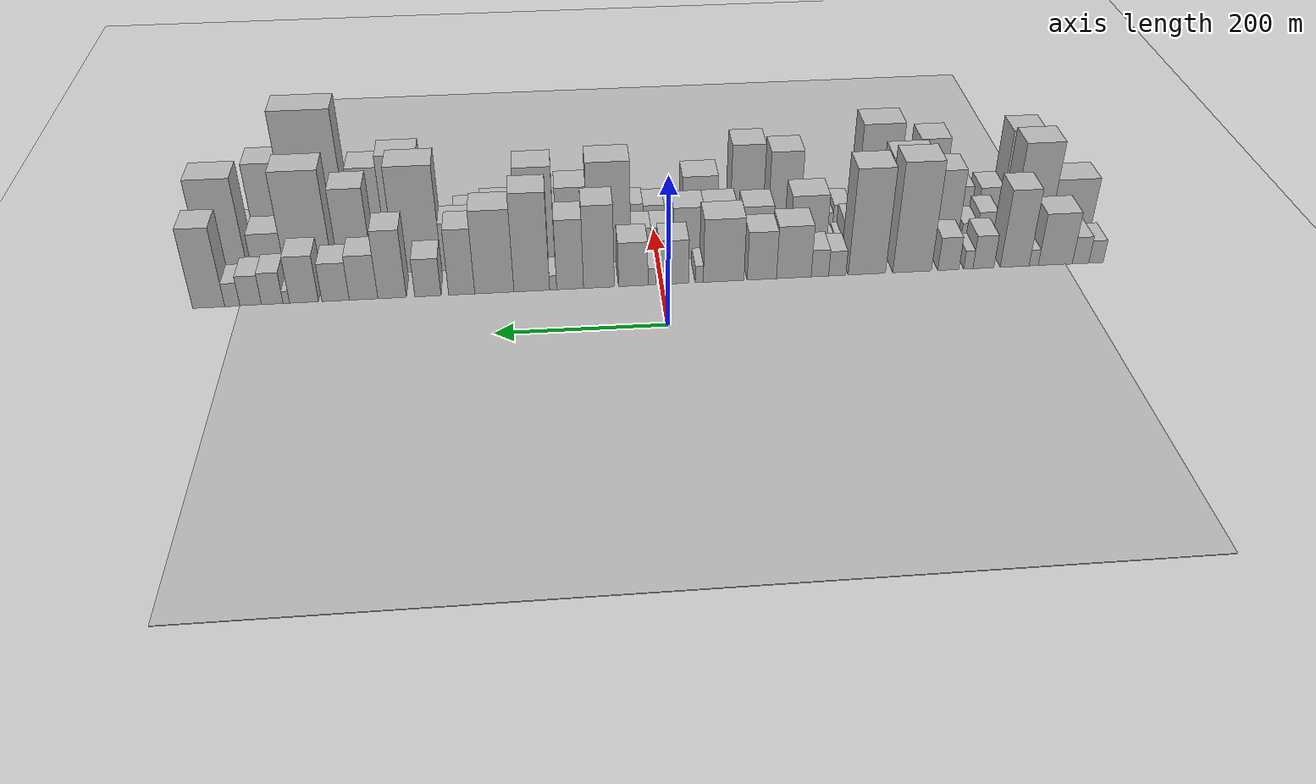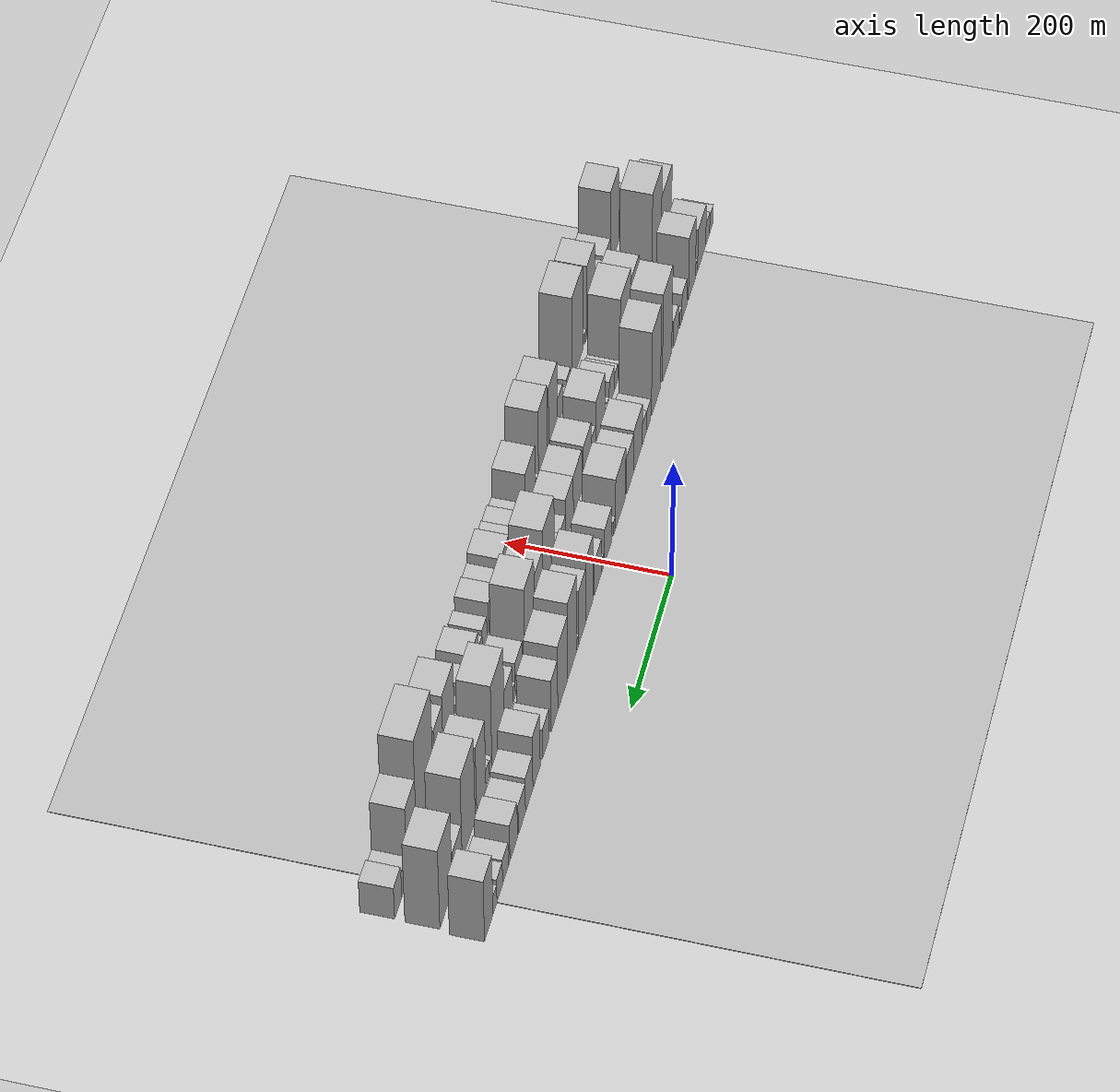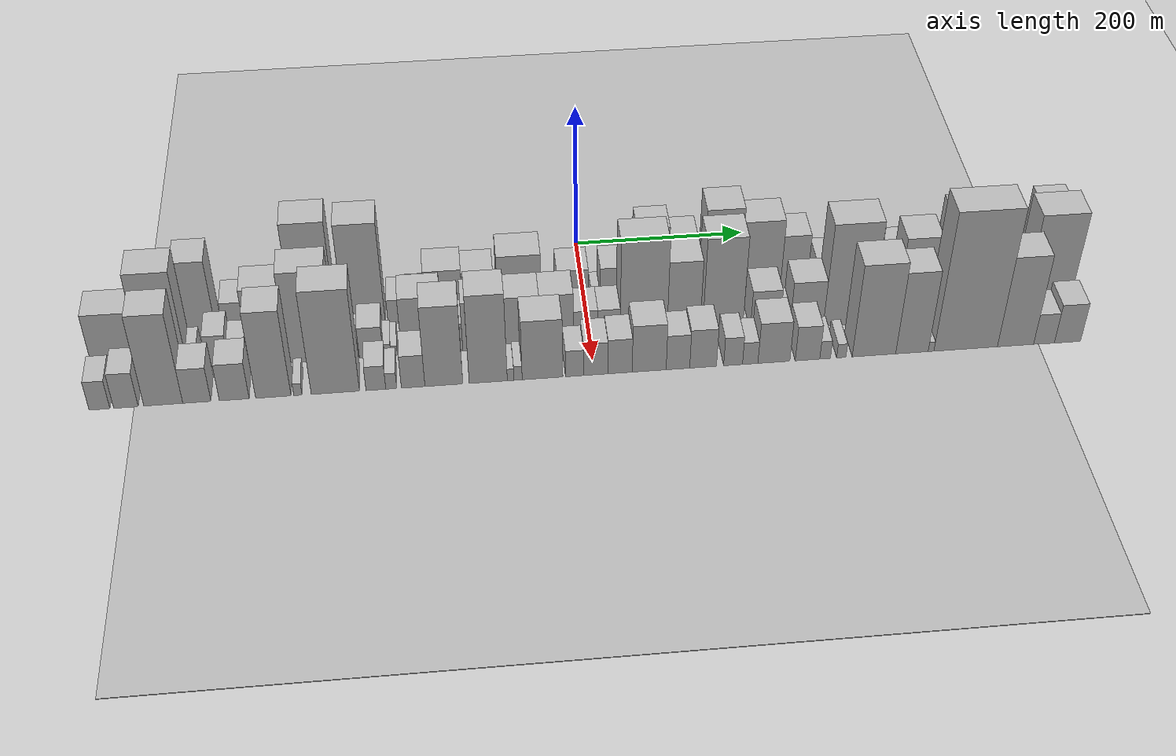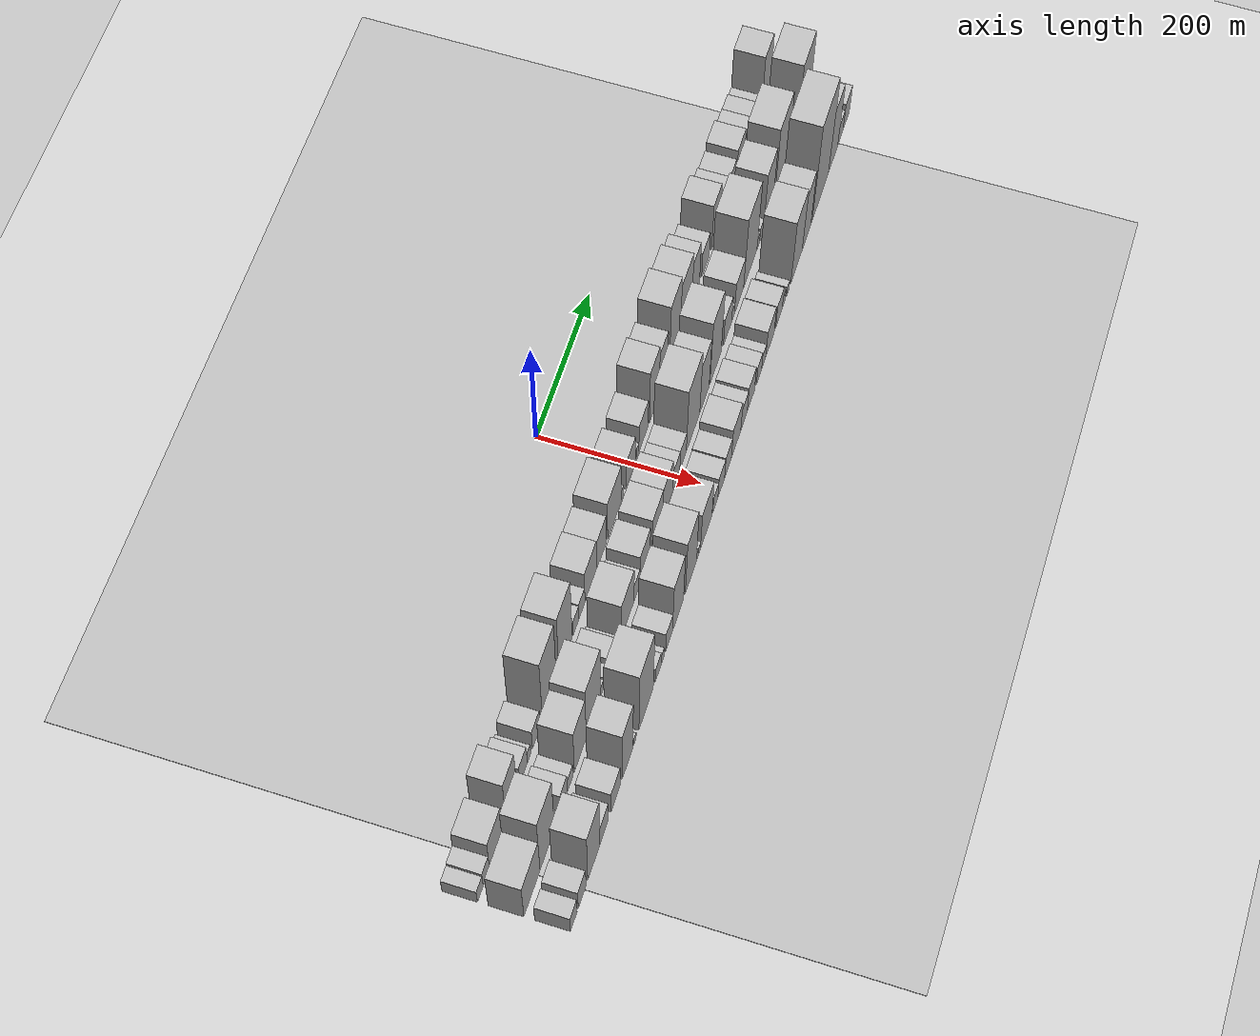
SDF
<?xml version="1.0" encoding="utf-8"?>

<sdf version="1.6">

   <world name="default">

      <gui fullscreen="0">

         <camera name="user_camera">

            <pose>-15 0 4.57585 0 0 0</pose>

            <view_controller>orbit</view_controller>

         </camera>

      </gui>

      <scene>

         <sky>

           <clouds>

             <speed>12</speed>

           </clouds>

         </sky>

         <ambient>0.4 0.4 0.4 1</ambient>

         <background>0.7 0.7 0.7 1</background>

         <shadows>1</shadows>

      </scene>

      <gravity>0 0 -9.8066</gravity>

      <magnetic_field>6e-06 2.3e-05 -4.2e-05</magnetic_field>

      <physics default="0" name="default_physics" type="ode">

         <ode>

            <solver>

               <type>quick</type>

               <iters>10</iters>

               <sor>1.0</sor>

               <use_dynamic_moi_rescaling>0</use_dynamic_moi_rescaling>

            </solver>

            <constraints>

               <cfm>0</cfm>

               <erp>0.2</erp>

               <contact_max_correcting_vel>100</contact_max_correcting_vel>

               <contact_surface_layer>0.001</contact_surface_layer>

            </constraints>

         </ode>

         <max_step_size>0.004</max_step_size>

         <real_time_factor>1</real_time_factor>

         <real_time_update_rate>250</real_time_update_rate>

      </physics>

      <light name="sun" type="directional">

         <cast_shadows>1</cast_shadows>

         <pose>0 0 10 0 0 0</pose>

         <diffuse>0.8 0.8 0.8 1</diffuse>

         <specular>0.2 0.2 0.2 1</specular>

         <attenuation>

            <range>1000</range>

            <constant>0.9</constant>

            <linear>0.01</linear>

            <quadratic>0.001</quadratic>

         </attenuation>

         <direction>-0.5 0.1 -0.9</direction>

      </light>

      <include>

         <name>ground_plane_1</name>

         <uri>model://HANNAS_ground_plane</uri>

         <pose>0 0 0  0 0 0</pose>

      </include>

      <include>

         <name>ground_plane_2</name>

         <uri>model://HANNAS_ground_plane</uri>

         <pose>100 0 0  0 0 0</pose>

      </include>

      <model name="building_1">

         <static>1</static>

         <pose frame="">100.0000 -538.8014 0 0.000000 0.000000 0.000000</pose>

         <link name="link">

            <pose frame="">0 0 16.50 0 0 0</pose>

            <collision name="collision">

               <geometry>

                  <box>

                     <size>40.0000 18.3971 33.0000</size>

                  </box>

               </geometry>

               <max_contacts>10</max_contacts>

               <surface>

                  <contact>

                     <ode/>

                  </contact>

                  <bounce/>

                  <friction>

                     <torsional>

                        <ode/>

                     </torsional>

                     <ode/>

                  </friction>

               </surface>

            </collision>

            <visual name="visual">

               <cast_shadows>0</cast_shadows>

               <geometry>

                  <box>

                     <size>40.0000 18.3971 33.0000</size>

                  </box>

               </geometry>

               <material>

                  <script>

                     <uri>model://HANNAS_wall/materials/scripts</uri>

                     <uri>model://HANNAS_wall/materials/textures</uri>

                     <name>vrc/HANNAS_wall</name>

                  </script>

               </material>

            </visual>

            <self_collide>0</self_collide>

            <enable_wind>0</enable_wind>

            <kinematic>0</kinematic>

         </link>

      </model>

      <model name="building_2">

         <static>1</static>

         <pose frame="">100.0000 -519.1855 0 0.000000 0.000000 0.000000</pose>

         <link name="link">

            <pose frame="">0 0 19.50 0 0 0</pose>

            <collision name="collision">

               <geometry>

                  <box>

                     <size>40.0000 20.8348 39.0000</size>

                  </box>

               </geometry>

               <max_contacts>10</max_contacts>

               <surface>

                  <contact>

                     <ode/>

                  </contact>

                  <bounce/>

                  <friction>

                     <torsional>

                        <ode/>

                     </torsional>

                     <ode/>

                  </friction>

               </surface>

            </collision>

            <visual name="visual">

               <cast_shadows>0</cast_shadows>

               <geometry>

                  <box>

                     <size>40.0000 20.8348 39.0000</size>

                  </box>

               </geometry>

               <material>

                  <script>

                     <uri>model://HANNAS_wall/materials/scripts</uri>

                     <uri>model://HANNAS_wall/materials/textures</uri>

                     <name>vrc/HANNAS_wall</name>

                  </script>

               </material>

            </visual>

            <self_collide>0</self_collide>

            <enable_wind>0</enable_wind>

            <kinematic>0</kinematic>

         </link>

      </model>

      <model name="building_3">

         <static>1</static>

         <pose frame="">100.0000 -487.1912 0 0.000000 0.000000 0.000000</pose>

         <link name="link">

            <pose frame="">0 0 37.50 0 0 0</pose>

            <collision name="collision">

               <geometry>

                  <box>

                     <size>40.0000 43.1539 75.0000</size>

                  </box>

               </geometry>

               <max_contacts>10</max_contacts>

               <surface>

                  <contact>

                     <ode/>

                  </contact>

                  <bounce/>

                  <friction>

                     <torsional>

                        <ode/>

                     </torsional>

                     <ode/>

                  </friction>

               </surface>

            </collision>

            <visual name="visual">

               <cast_shadows>0</cast_shadows>

               <geometry>

                  <box>

                     <size>40.0000 43.1539 75.0000</size>

                  </box>

               </geometry>

               <material>

                  <script>

                     <uri>model://HANNAS_wall/materials/scripts</uri>

                     <uri>model://HANNAS_wall/materials/textures</uri>

                     <name>vrc/HANNAS_wall</name>

                  </script>

               </material>

            </visual>

            <self_collide>0</self_collide>

            <enable_wind>0</enable_wind>

            <kinematic>0</kinematic>

         </link>

      </model>

      <model name="building_4">

         <static>1</static>

         <pose frame="">100.0000 -459.8287 0 0.000000 0.000000 0.000000</pose>

         <link name="link">

            <pose frame="">0 0 12.00 0 0 0</pose>

            <collision name="collision">

               <geometry>

                  <box>

                     <size>40.0000 11.5711 24.0000</size>

                  </box>

               </geometry>

               <max_contacts>10</max_contacts>

               <surface>

                  <contact>

                     <ode/>

                  </contact>

                  <bounce/>

                  <friction>

                     <torsional>

                        <ode/>

                     </torsional>

                     <ode/>

                  </friction>

               </surface>

            </collision>

            <visual name="visual">

               <cast_shadows>0</cast_shadows>

               <geometry>

                  <box>

                     <size>40.0000 11.5711 24.0000</size>

                  </box>

               </geometry>

               <material>

                  <script>

                     <uri>model://HANNAS_wall/materials/scripts</uri>

                     <uri>model://HANNAS_wall/materials/textures</uri>

                     <name>vrc/HANNAS_wall</name>

                  </script>

               </material>

            </visual>

            <self_collide>0</self_collide>

            <enable_wind>0</enable_wind>

            <kinematic>0</kinematic>

         </link>

      </model>

      <model name="building_5">

         <static>1</static>

         <pose frame="">100.0000 -435.8824 0 0.000000 0.000000 0.000000</pose>

         <link name="link">

            <pose frame="">0 0 55.50 0 0 0</pose>

            <collision name="collision">

               <geometry>

                  <box>

                     <size>40.0000 36.3215 111.0000</size>

                  </box>

               </geometry>

               <max_contacts>10</max_contacts>

               <surface>

                  <contact>

                     <ode/>

                  </contact>

                  <bounce/>

                  <friction>

                     <torsional>

                        <ode/>

                     </torsional>

                     <ode/>

                  </friction>

               </surface>

            </collision>

            <visual name="visual">

               <cast_shadows>0</cast_shadows>

               <geometry>

                  <box>

                     <size>40.0000 36.3215 111.0000</size>

                  </box>

               </geometry>

               <material>

                  <script>

                     <uri>model://HANNAS_wall/materials/scripts</uri>

                     <uri>model://HANNAS_wall/materials/textures</uri>

                     <name>vrc/HANNAS_wall</name>

                  </script>

               </material>

            </visual>

            <self_collide>0</self_collide>

            <enable_wind>0</enable_wind>

            <kinematic>0</kinematic>

         </link>

      </model>

      <model name="building_6">

         <static>1</static>

         <pose frame="">100.0000 -396.5858 0 0.000000 0.000000 0.000000</pose>

         <link name="link">

            <pose frame="">0 0 24.00 0 0 0</pose>

            <collision name="collision">

               <geometry>

                  <box>

                     <size>40.0000 26.2716 48.0000</size>

                  </box>

               </geometry>

               <max_contacts>10</max_contacts>

               <surface>

                  <contact>

                     <ode/>

                  </contact>

                  <bounce/>

                  <friction>

                     <torsional>

                        <ode/>

                     </torsional>

                     <ode/>

                  </friction>

               </surface>

            </collision>

            <visual name="visual">

               <cast_shadows>0</cast_shadows>

               <geometry>

                  <box>

                     <size>40.0000 26.2716 48.0000</size>

                  </box>

               </geometry>

               <material>

                  <script>

                     <uri>model://HANNAS_wall/materials/scripts</uri>

                     <uri>model://HANNAS_wall/materials/textures</uri>

                     <name>vrc/HANNAS_wall</name>

                  </script>

               </material>

            </visual>

            <self_collide>0</self_collide>

            <enable_wind>0</enable_wind>

            <kinematic>0</kinematic>

         </link>

      </model>

      <model name="building_7">

         <static>1</static>

         <pose frame="">100.0000 -377.6897 0 0.000000 0.000000 0.000000</pose>

         <link name="link">

            <pose frame="">0 0 13.50 0 0 0</pose>

            <collision name="collision">

               <geometry>

                  <box>

                     <size>40.0000 11.5206 27.0000</size>

                  </box>

               </geometry>

               <max_contacts>10</max_contacts>

               <surface>

                  <contact>

                     <ode/>

                  </contact>

                  <bounce/>

                  <friction>

                     <torsional>

                        <ode/>

                     </torsional>

                     <ode/>

                  </friction>

               </surface>

            </collision>

            <visual name="visual">

               <cast_shadows>0</cast_shadows>

               <geometry>

                  <box>

                     <size>40.0000 11.5206 27.0000</size>

                  </box>

               </geometry>

               <material>

                  <script>

                     <uri>model://HANNAS_wall/materials/scripts</uri>

                     <uri>model://HANNAS_wall/materials/textures</uri>

                     <name>vrc/HANNAS_wall</name>

                  </script>

               </material>

            </visual>

            <self_collide>0</self_collide>

            <enable_wind>0</enable_wind>

            <kinematic>0</kinematic>

         </link>

      </model>

      <model name="building_8">

         <static>1</static>

         <pose frame="">100.0000 -352.7261 0 0.000000 0.000000 0.000000</pose>

         <link name="link">

            <pose frame="">0 0 24.00 0 0 0</pose>

            <collision name="collision">

               <geometry>

                  <box>

                     <size>40.0000 26.4067 48.0000</size>

                  </box>

               </geometry>

               <max_contacts>10</max_contacts>

               <surface>

                  <contact>

                     <ode/>

                  </contact>

                  <bounce/>

                  <friction>

                     <torsional>

                        <ode/>

                     </torsional>

                     <ode/>

                  </friction>

               </surface>

            </collision>

            <visual name="visual">

               <cast_shadows>0</cast_shadows>

               <geometry>

                  <box>

                     <size>40.0000 26.4067 48.0000</size>

                  </box>

               </geometry>

               <material>

                  <script>

                     <uri>model://HANNAS_wall/materials/scripts</uri>

                     <uri>model://HANNAS_wall/materials/textures</uri>

                     <name>vrc/HANNAS_wall</name>

                  </script>

               </material>

            </visual>

            <self_collide>0</self_collide>

            <enable_wind>0</enable_wind>

            <kinematic>0</kinematic>

         </link>

      </model>

      <model name="building_9">

         <static>1</static>

         <pose frame="">100.0000 -307.4789 0 0.000000 0.000000 0.000000</pose>

         <link name="link">

            <pose frame="">0 0 78.00 0 0 0</pose>

            <collision name="collision">

               <geometry>

                  <box>

                     <size>40.0000 48.0877 156.0000</size>

                  </box>

               </geometry>

               <max_contacts>10</max_contacts>

               <surface>

                  <contact>

                     <ode/>

                  </contact>

                  <bounce/>

                  <friction>

                     <torsional>

                        <ode/>

                     </torsional>

                     <ode/>

                  </friction>

               </surface>

            </collision>

            <visual name="visual">

               <cast_shadows>0</cast_shadows>

               <geometry>

                  <box>

                     <size>40.0000 48.0877 156.0000</size>

                  </box>

               </geometry>

               <material>

                  <script>

                     <uri>model://HANNAS_wall/materials/scripts</uri>

                     <uri>model://HANNAS_wall/materials/textures</uri>

                     <name>vrc/HANNAS_wall</name>

                  </script>

               </material>

            </visual>

            <self_collide>0</self_collide>

            <enable_wind>0</enable_wind>

            <kinematic>0</kinematic>

         </link>

      </model>

      <model name="building_10">

         <static>1</static>

         <pose frame="">100.0000 -251.3428 0 0.000000 0.000000 0.000000</pose>

         <link name="link">

            <pose frame="">0 0 75.00 0 0 0</pose>

            <collision name="collision">

               <geometry>

                  <box>

                     <size>40.0000 46.1845 150.0000</size>

                  </box>

               </geometry>

               <max_contacts>10</max_contacts>

               <surface>

                  <contact>

                     <ode/>

                  </contact>

                  <bounce/>

                  <friction>

                     <torsional>

                        <ode/>

                     </torsional>

                     <ode/>

                  </friction>

               </surface>

            </collision>

            <visual name="visual">

               <cast_shadows>0</cast_shadows>

               <geometry>

                  <box>

                     <size>40.0000 46.1845 150.0000</size>

                  </box>

               </geometry>

               <material>

                  <script>

                     <uri>model://HANNAS_wall/materials/scripts</uri>

                     <uri>model://HANNAS_wall/materials/textures</uri>

                     <name>vrc/HANNAS_wall</name>

                  </script>

               </material>

            </visual>

            <self_collide>0</self_collide>

            <enable_wind>0</enable_wind>

            <kinematic>0</kinematic>

         </link>

      </model>

      <model name="building_11">

         <static>1</static>

         <pose frame="">100.0000 -214.6620 0 0.000000 0.000000 0.000000</pose>

         <link name="link">

            <pose frame="">0 0 18.00 0 0 0</pose>

            <collision name="collision">

               <geometry>

                  <box>

                     <size>40.0000 21.1770 36.0000</size>

                  </box>

               </geometry>

               <max_contacts>10</max_contacts>

               <surface>

                  <contact>

                     <ode/>

                  </contact>

                  <bounce/>

                  <friction>

                     <torsional>

                        <ode/>

                     </torsional>

                     <ode/>

                  </friction>

               </surface>

            </collision>

            <visual name="visual">

               <cast_shadows>0</cast_shadows>

               <geometry>

                  <box>

                     <size>40.0000 21.1770 36.0000</size>

                  </box>

               </geometry>

               <material>

                  <script>

                     <uri>model://HANNAS_wall/materials/scripts</uri>

                     <uri>model://HANNAS_wall/materials/textures</uri>

                     <name>vrc/HANNAS_wall</name>

                  </script>

               </material>

            </visual>

            <self_collide>0</self_collide>

            <enable_wind>0</enable_wind>

            <kinematic>0</kinematic>

         </link>

      </model>

      <model name="building_12">

         <static>1</static>

         <pose frame="">100.0000 -193.2816 0 0.000000 0.000000 0.000000</pose>

         <link name="link">

            <pose frame="">0 0 19.50 0 0 0</pose>

            <collision name="collision">

               <geometry>

                  <box>

                     <size>40.0000 21.5837 39.0000</size>

                  </box>

               </geometry>

               <max_contacts>10</max_contacts>

               <surface>

                  <contact>

                     <ode/>

                  </contact>

                  <bounce/>

                  <friction>

                     <torsional>

                        <ode/>

                     </torsional>

                     <ode/>

                  </friction>

               </surface>

            </collision>

            <visual name="visual">

               <cast_shadows>0</cast_shadows>

               <geometry>

                  <box>

                     <size>40.0000 21.5837 39.0000</size>

                  </box>

               </geometry>

               <material>

                  <script>

                     <uri>model://HANNAS_wall/materials/scripts</uri>

                     <uri>model://HANNAS_wall/materials/textures</uri>

                     <name>vrc/HANNAS_wall</name>

                  </script>

               </material>

            </visual>

            <self_collide>0</self_collide>

            <enable_wind>0</enable_wind>

            <kinematic>0</kinematic>

         </link>

      </model>

      <model name="building_13">

         <static>1</static>

         <pose frame="">100.0000 -161.1651 0 0.000000 0.000000 0.000000</pose>

         <link name="link">

            <pose frame="">0 0 37.50 0 0 0</pose>

            <collision name="collision">

               <geometry>

                  <box>

                     <size>40.0000 42.6494 75.0000</size>

                  </box>

               </geometry>

               <max_contacts>10</max_contacts>

               <surface>

                  <contact>

                     <ode/>

                  </contact>

                  <bounce/>

                  <friction>

                     <torsional>

                        <ode/>

                     </torsional>

                     <ode/>

                  </friction>

               </surface>

            </collision>

            <visual name="visual">

               <cast_shadows>0</cast_shadows>

               <geometry>

                  <box>

                     <size>40.0000 42.6494 75.0000</size>

                  </box>

               </geometry>

               <material>

                  <script>

                     <uri>model://HANNAS_wall/materials/scripts</uri>

                     <uri>model://HANNAS_wall/materials/textures</uri>

                     <name>vrc/HANNAS_wall</name>

                  </script>

               </material>

            </visual>

            <self_collide>0</self_collide>

            <enable_wind>0</enable_wind>

            <kinematic>0</kinematic>

         </link>

      </model>

      <model name="building_14">

         <static>1</static>

         <pose frame="">100.0000 -121.9393 0 0.000000 0.000000 0.000000</pose>

         <link name="link">

            <pose frame="">0 0 34.50 0 0 0</pose>

            <collision name="collision">

               <geometry>

                  <box>

                     <size>40.0000 35.8023 69.0000</size>

                  </box>

               </geometry>

               <max_contacts>10</max_contacts>

               <surface>

                  <contact>

                     <ode/>

                  </contact>

                  <bounce/>

                  <friction>

                     <torsional>

                        <ode/>

                     </torsional>

                     <ode/>

                  </friction>

               </surface>

            </collision>

            <visual name="visual">

               <cast_shadows>0</cast_shadows>

               <geometry>

                  <box>

                     <size>40.0000 35.8023 69.0000</size>

                  </box>

               </geometry>

               <material>

                  <script>

                     <uri>model://HANNAS_wall/materials/scripts</uri>

                     <uri>model://HANNAS_wall/materials/textures</uri>

                     <name>vrc/HANNAS_wall</name>

                  </script>

               </material>

            </visual>

            <self_collide>0</self_collide>

            <enable_wind>0</enable_wind>

            <kinematic>0</kinematic>

         </link>

      </model>

      <model name="building_15">

         <static>1</static>

         <pose frame="">100.0000 -75.2578 0 0.000000 0.000000 0.000000</pose>

         <link name="link">

            <pose frame="">0 0 45.00 0 0 0</pose>

            <collision name="collision">

               <geometry>

                  <box>

                     <size>40.0000 49.5606 90.0000</size>

                  </box>

               </geometry>

               <max_contacts>10</max_contacts>

               <surface>

                  <contact>

                     <ode/>

                  </contact>

                  <bounce/>

                  <friction>

                     <torsional>

                        <ode/>

                     </torsional>

                     <ode/>

                  </friction>

               </surface>

            </collision>

            <visual name="visual">

               <cast_shadows>0</cast_shadows>

               <geometry>

                  <box>

                     <size>40.0000 49.5606 90.0000</size>

                  </box>

               </geometry>

               <material>

                  <script>

                     <uri>model://HANNAS_wall/materials/scripts</uri>

                     <uri>model://HANNAS_wall/materials/textures</uri>

                     <name>vrc/HANNAS_wall</name>

                  </script>

               </material>

            </visual>

            <self_collide>0</self_collide>

            <enable_wind>0</enable_wind>

            <kinematic>0</kinematic>

         </link>

      </model>

      <model name="building_16">

         <static>1</static>

         <pose frame="">100.0000 -45.5275 0 0.000000 0.000000 0.000000</pose>

         <link name="link">

            <pose frame="">0 0 12.00 0 0 0</pose>

            <collision name="collision">

               <geometry>

                  <box>

                     <size>40.0000 9.9000 24.0000</size>

                  </box>

               </geometry>

               <max_contacts>10</max_contacts>

               <surface>

                  <contact>

                     <ode/>

                  </contact>

                  <bounce/>

                  <friction>

                     <torsional>

                        <ode/>

                     </torsional>

                     <ode/>

                  </friction>

               </surface>

            </collision>

            <visual name="visual">

               <cast_shadows>0</cast_shadows>

               <geometry>

                  <box>

                     <size>40.0000 9.9000 24.0000</size>

                  </box>

               </geometry>

               <material>

                  <script>

                     <uri>model://HANNAS_wall/materials/scripts</uri>

                     <uri>model://HANNAS_wall/materials/textures</uri>

                     <name>vrc/HANNAS_wall</name>

                  </script>

               </material>

            </visual>

            <self_collide>0</self_collide>

            <enable_wind>0</enable_wind>

            <kinematic>0</kinematic>

         </link>

      </model>

      <model name="building_17">

         <static>1</static>

         <pose frame="">100.0000 -14.7085 0 0.000000 0.000000 0.000000</pose>

         <link name="link">

            <pose frame="">0 0 31.50 0 0 0</pose>

            <collision name="collision">

               <geometry>

                  <box>

                     <size>40.0000 35.7380 63.0000</size>

                  </box>

               </geometry>

               <max_contacts>10</max_contacts>

               <surface>

                  <contact>

                     <ode/>

                  </contact>

                  <bounce/>

                  <friction>

                     <torsional>

                        <ode/>

                     </torsional>

                     <ode/>

                  </friction>

               </surface>

            </collision>

            <visual name="visual">

               <cast_shadows>0</cast_shadows>

               <geometry>

                  <box>

                     <size>40.0000 35.7380 63.0000</size>

                  </box>

               </geometry>

               <material>

                  <script>

                     <uri>model://HANNAS_wall/materials/scripts</uri>

                     <uri>model://HANNAS_wall/materials/textures</uri>

                     <name>vrc/HANNAS_wall</name>

                  </script>

               </material>

            </visual>

            <self_collide>0</self_collide>

            <enable_wind>0</enable_wind>

            <kinematic>0</kinematic>

         </link>

      </model>

      <model name="building_18">

         <static>1</static>

         <pose frame="">100.0000 11.9810 0 0.000000 0.000000 0.000000</pose>

         <link name="link">

            <pose frame="">0 0 12.00 0 0 0</pose>

            <collision name="collision">

               <geometry>

                  <box>

                     <size>40.0000 9.6409 24.0000</size>

                  </box>

               </geometry>

               <max_contacts>10</max_contacts>

               <surface>

                  <contact>

                     <ode/>

                  </contact>

                  <bounce/>

                  <friction>

                     <torsional>

                        <ode/>

                     </torsional>

                     <ode/>

                  </friction>

               </surface>

            </collision>

            <visual name="visual">

               <cast_shadows>0</cast_shadows>

               <geometry>

                  <box>

                     <size>40.0000 9.6409 24.0000</size>

                  </box>

               </geometry>

               <material>

                  <script>

                     <uri>model://HANNAS_wall/materials/scripts</uri>

                     <uri>model://HANNAS_wall/materials/textures</uri>

                     <name>vrc/HANNAS_wall</name>

                  </script>

               </material>

            </visual>

            <self_collide>0</self_collide>

            <enable_wind>0</enable_wind>

            <kinematic>0</kinematic>

         </link>

      </model>

      <model name="building_19">

         <static>1</static>

         <pose frame="">100.0000 34.5538 0 0.000000 0.000000 0.000000</pose>

         <link name="link">

            <pose frame="">0 0 31.50 0 0 0</pose>

            <collision name="collision">

               <geometry>

                  <box>

                     <size>40.0000 35.5048 63.0000</size>

                  </box>

               </geometry>

               <max_contacts>10</max_contacts>

               <surface>

                  <contact>

                     <ode/>

                  </contact>

                  <bounce/>

                  <friction>

                     <torsional>

                        <ode/>

                     </torsional>

                     <ode/>

                  </friction>

               </surface>

            </collision>

            <visual name="visual">

               <cast_shadows>0</cast_shadows>

               <geometry>

                  <box>

                     <size>40.0000 35.5048 63.0000</size>

                  </box>

               </geometry>

               <material>

                  <script>

                     <uri>model://HANNAS_wall/materials/scripts</uri>

                     <uri>model://HANNAS_wall/materials/textures</uri>

                     <name>vrc/HANNAS_wall</name>

                  </script>

               </material>

            </visual>

            <self_collide>0</self_collide>

            <enable_wind>0</enable_wind>

            <kinematic>0</kinematic>

         </link>

      </model>

      <model name="building_20">

         <static>1</static>

         <pose frame="">100.0000 75.8452 0 0.000000 0.000000 0.000000</pose>

         <link name="link">

            <pose frame="">0 0 58.50 0 0 0</pose>

            <collision name="collision">

               <geometry>

                  <box>

                     <size>40.0000 37.0780 117.0000</size>

                  </box>

               </geometry>

               <max_contacts>10</max_contacts>

               <surface>

                  <contact>

                     <ode/>

                  </contact>

                  <bounce/>

                  <friction>

                     <torsional>

                        <ode/>

                     </torsional>

                     <ode/>

                  </friction>

               </surface>

            </collision>

            <visual name="visual">

               <cast_shadows>0</cast_shadows>

               <geometry>

                  <box>

                     <size>40.0000 37.0780 117.0000</size>

                  </box>

               </geometry>

               <material>

                  <script>

                     <uri>model://HANNAS_wall/materials/scripts</uri>

                     <uri>model://HANNAS_wall/materials/textures</uri>

                     <name>vrc/HANNAS_wall</name>

                  </script>

               </material>

            </visual>

            <self_collide>0</self_collide>

            <enable_wind>0</enable_wind>

            <kinematic>0</kinematic>

         </link>

      </model>

      <model name="building_21">

         <static>1</static>

         <pose frame="">100.0000 110.5183 0 0.000000 0.000000 0.000000</pose>

         <link name="link">

            <pose frame="">0 0 49.50 0 0 0</pose>

            <collision name="collision">

               <geometry>

                  <box>

                     <size>40.0000 32.2683 99.0000</size>

                  </box>

               </geometry>

               <max_contacts>10</max_contacts>

               <surface>

                  <contact>

                     <ode/>

                  </contact>

                  <bounce/>

                  <friction>

                     <torsional>

                        <ode/>

                     </torsional>

                     <ode/>

                  </friction>

               </surface>

            </collision>

            <visual name="visual">

               <cast_shadows>0</cast_shadows>

               <geometry>

                  <box>

                     <size>40.0000 32.2683 99.0000</size>

                  </box>

               </geometry>

               <material>

                  <script>

                     <uri>model://HANNAS_wall/materials/scripts</uri>

                     <uri>model://HANNAS_wall/materials/textures</uri>

                     <name>vrc/HANNAS_wall</name>

                  </script>

               </material>

            </visual>

            <self_collide>0</self_collide>

            <enable_wind>0</enable_wind>

            <kinematic>0</kinematic>

         </link>

      </model>

      <model name="building_22">

         <static>1</static>

         <pose frame="">100.0000 130.8560 0 0.000000 0.000000 0.000000</pose>

         <link name="link">

            <pose frame="">0 0 10.50 0 0 0</pose>

            <collision name="collision">

               <geometry>

                  <box>

                     <size>40.0000 8.4071 21.0000</size>

                  </box>

               </geometry>

               <max_contacts>10</max_contacts>

               <surface>

                  <contact>

                     <ode/>

                  </contact>

                  <bounce/>

                  <friction>

                     <torsional>

                        <ode/>

                     </torsional>

                     <ode/>

                  </friction>

               </surface>

            </collision>

            <visual name="visual">

               <cast_shadows>0</cast_shadows>

               <geometry>

                  <box>

                     <size>40.0000 8.4071 21.0000</size>

                  </box>

               </geometry>

               <material>

                  <script>

                     <uri>model://HANNAS_wall/materials/scripts</uri>

                     <uri>model://HANNAS_wall/materials/textures</uri>

                     <name>vrc/HANNAS_wall</name>

                  </script>

               </material>

            </visual>

            <self_collide>0</self_collide>

            <enable_wind>0</enable_wind>

            <kinematic>0</kinematic>

         </link>

      </model>

      <model name="building_23">

         <static>1</static>

         <pose frame="">100.0000 156.3735 0 0.000000 0.000000 0.000000</pose>

         <link name="link">

            <pose frame="">0 0 69.00 0 0 0</pose>

            <collision name="collision">

               <geometry>

                  <box>

                     <size>40.0000 42.6278 138.0000</size>

                  </box>

               </geometry>

               <max_contacts>10</max_contacts>

               <surface>

                  <contact>

                     <ode/>

                  </contact>

                  <bounce/>

                  <friction>

                     <torsional>

                        <ode/>

                     </torsional>

                     <ode/>

                  </friction>

               </surface>

            </collision>

            <visual name="visual">

               <cast_shadows>0</cast_shadows>

               <geometry>

                  <box>

                     <size>40.0000 42.6278 138.0000</size>

                  </box>

               </geometry>

               <material>

                  <script>

                     <uri>model://HANNAS_wall/materials/scripts</uri>

                     <uri>model://HANNAS_wall/materials/textures</uri>

                     <name>vrc/HANNAS_wall</name>

                  </script>

               </material>

            </visual>

            <self_collide>0</self_collide>

            <enable_wind>0</enable_wind>

            <kinematic>0</kinematic>

         </link>

      </model>

      <model name="building_24">

         <static>1</static>

         <pose frame="">100.0000 201.0394 0 0.000000 0.000000 0.000000</pose>

         <link name="link">

            <pose frame="">0 0 58.50 0 0 0</pose>

            <collision name="collision">

               <geometry>

                  <box>

                     <size>40.0000 46.7040 117.0000</size>

                  </box>

               </geometry>

               <max_contacts>10</max_contacts>

               <surface>

                  <contact>

                     <ode/>

                  </contact>

                  <bounce/>

                  <friction>

                     <torsional>

                        <ode/>

                     </torsional>

                     <ode/>

                  </friction>

               </surface>

            </collision>

            <visual name="visual">

               <cast_shadows>0</cast_shadows>

               <geometry>

                  <box>

                     <size>40.0000 46.7040 117.0000</size>

                  </box>

               </geometry>

               <material>

                  <script>

                     <uri>model://HANNAS_wall/materials/scripts</uri>

                     <uri>model://HANNAS_wall/materials/textures</uri>

                     <name>vrc/HANNAS_wall</name>

                  </script>

               </material>

            </visual>

            <self_collide>0</self_collide>

            <enable_wind>0</enable_wind>

            <kinematic>0</kinematic>

         </link>

      </model>

      <model name="building_25">

         <static>1</static>

         <pose frame="">100.0000 239.8591 0 0.000000 0.000000 0.000000</pose>

         <link name="link">

            <pose frame="">0 0 46.50 0 0 0</pose>

            <collision name="collision">

               <geometry>

                  <box>

                     <size>40.0000 30.9353 93.0000</size>

                  </box>

               </geometry>

               <max_contacts>10</max_contacts>

               <surface>

                  <contact>

                     <ode/>

                  </contact>

                  <bounce/>

                  <friction>

                     <torsional>

                        <ode/>

                     </torsional>

                     <ode/>

                  </friction>

               </surface>

            </collision>

            <visual name="visual">

               <cast_shadows>0</cast_shadows>

               <geometry>

                  <box>

                     <size>40.0000 30.9353 93.0000</size>

                  </box>

               </geometry>

               <material>

                  <script>

                     <uri>model://HANNAS_wall/materials/scripts</uri>

                     <uri>model://HANNAS_wall/materials/textures</uri>

                     <name>vrc/HANNAS_wall</name>

                  </script>

               </material>

            </visual>

            <self_collide>0</self_collide>

            <enable_wind>0</enable_wind>

            <kinematic>0</kinematic>

         </link>

      </model>

      <model name="building_26">

         <static>1</static>

         <pose frame="">100.0000 279.8218 0 0.000000 0.000000 0.000000</pose>

         <link name="link">

            <pose frame="">0 0 27.00 0 0 0</pose>

            <collision name="collision">

               <geometry>

                  <box>

                     <size>40.0000 30.9903 54.0000</size>

                  </box>

               </geometry>

               <max_contacts>10</max_contacts>

               <surface>

                  <contact>

                     <ode/>

                  </contact>

                  <bounce/>

                  <friction>

                     <torsional>

                        <ode/>

                     </torsional>

                     <ode/>

                  </friction>

               </surface>

            </collision>

            <visual name="visual">

               <cast_shadows>0</cast_shadows>

               <geometry>

                  <box>

                     <size>40.0000 30.9903 54.0000</size>

                  </box>

               </geometry>

               <material>

                  <script>

                     <uri>model://HANNAS_wall/materials/scripts</uri>

                     <uri>model://HANNAS_wall/materials/textures</uri>

                     <name>vrc/HANNAS_wall</name>

                  </script>

               </material>

            </visual>

            <self_collide>0</self_collide>

            <enable_wind>0</enable_wind>

            <kinematic>0</kinematic>

         </link>

      </model>

      <model name="building_27">

         <static>1</static>

         <pose frame="">100.0000 322.0922 0 0.000000 0.000000 0.000000</pose>

         <link name="link">

            <pose frame="">0 0 48.00 0 0 0</pose>

            <collision name="collision">

               <geometry>

                  <box>

                     <size>40.0000 33.5505 96.0000</size>

                  </box>

               </geometry>

               <max_contacts>10</max_contacts>

               <surface>

                  <contact>

                     <ode/>

                  </contact>

                  <bounce/>

                  <friction>

                     <torsional>

                        <ode/>

                     </torsional>

                     <ode/>

                  </friction>

               </surface>

            </collision>

            <visual name="visual">

               <cast_shadows>0</cast_shadows>

               <geometry>

                  <box>

                     <size>40.0000 33.5505 96.0000</size>

                  </box>

               </geometry>

               <material>

                  <script>

                     <uri>model://HANNAS_wall/materials/scripts</uri>

                     <uri>model://HANNAS_wall/materials/textures</uri>

                     <name>vrc/HANNAS_wall</name>

                  </script>

               </material>

            </visual>

            <self_collide>0</self_collide>

            <enable_wind>0</enable_wind>

            <kinematic>0</kinematic>

         </link>

      </model>

      <model name="building_28">

         <static>1</static>

         <pose frame="">100.0000 355.6027 0 0.000000 0.000000 0.000000</pose>

         <link name="link">

            <pose frame="">0 0 31.50 0 0 0</pose>

            <collision name="collision">

               <geometry>

                  <box>

                     <size>40.0000 33.4706 63.0000</size>

                  </box>

               </geometry>

               <max_contacts>10</max_contacts>

               <surface>

                  <contact>

                     <ode/>

                  </contact>

                  <bounce/>

                  <friction>

                     <torsional>

                        <ode/>

                     </torsional>

                     <ode/>

                  </friction>

               </surface>

            </collision>

            <visual name="visual">

               <cast_shadows>0</cast_shadows>

               <geometry>

                  <box>

                     <size>40.0000 33.4706 63.0000</size>

                  </box>

               </geometry>

               <material>

                  <script>

                     <uri>model://HANNAS_wall/materials/scripts</uri>

                     <uri>model://HANNAS_wall/materials/textures</uri>

                     <name>vrc/HANNAS_wall</name>

                  </script>

               </material>

            </visual>

            <self_collide>0</self_collide>

            <enable_wind>0</enable_wind>

            <kinematic>0</kinematic>

         </link>

      </model>

      <model name="building_29">

         <static>1</static>

         <pose frame="">100.0000 388.4130 0 0.000000 0.000000 0.000000</pose>

         <link name="link">

            <pose frame="">0 0 27.00 0 0 0</pose>

            <collision name="collision">

               <geometry>

                  <box>

                     <size>40.0000 32.1499 54.0000</size>

                  </box>

               </geometry>

               <max_contacts>10</max_contacts>

               <surface>

                  <contact>

                     <ode/>

                  </contact>

                  <bounce/>

                  <friction>

                     <torsional>

                        <ode/>

                     </torsional>

                     <ode/>

                  </friction>

               </surface>

            </collision>

            <visual name="visual">

               <cast_shadows>0</cast_shadows>

               <geometry>

                  <box>

                     <size>40.0000 32.1499 54.0000</size>

                  </box>

               </geometry>

               <material>

                  <script>

                     <uri>model://HANNAS_wall/materials/scripts</uri>

                     <uri>model://HANNAS_wall/materials/textures</uri>

                     <name>vrc/HANNAS_wall</name>

                  </script>

               </material>

            </visual>

            <self_collide>0</self_collide>

            <enable_wind>0</enable_wind>

            <kinematic>0</kinematic>

         </link>

      </model>

      <model name="building_30">

         <static>1</static>

         <pose frame="">100.0000 425.3685 0 0.000000 0.000000 0.000000</pose>

         <link name="link">

            <pose frame="">0 0 33.00 0 0 0</pose>

            <collision name="collision">

               <geometry>

                  <box>

                     <size>40.0000 33.7612 66.0000</size>

                  </box>

               </geometry>

               <max_contacts>10</max_contacts>

               <surface>

                  <contact>

                     <ode/>

                  </contact>

                  <bounce/>

                  <friction>

                     <torsional>

                        <ode/>

                     </torsional>

                     <ode/>

                  </friction>

               </surface>

            </collision>

            <visual name="visual">

               <cast_shadows>0</cast_shadows>

               <geometry>

                  <box>

                     <size>40.0000 33.7612 66.0000</size>

                  </box>

               </geometry>

               <material>

                  <script>

                     <uri>model://HANNAS_wall/materials/scripts</uri>

                     <uri>model://HANNAS_wall/materials/textures</uri>

                     <name>vrc/HANNAS_wall</name>

                  </script>

               </material>

            </visual>

            <self_collide>0</self_collide>

            <enable_wind>0</enable_wind>

            <kinematic>0</kinematic>

         </link>

      </model>

      <model name="building_31">

         <static>1</static>

         <pose frame="">100.0000 445.9851 0 0.000000 0.000000 0.000000</pose>

         <link name="link">

            <pose frame="">0 0 9.00 0 0 0</pose>

            <collision name="collision">

               <geometry>

                  <box>

                     <size>40.0000 7.4719 18.0000</size>

                  </box>

               </geometry>

               <max_contacts>10</max_contacts>

               <surface>

                  <contact>

                     <ode/>

                  </contact>

                  <bounce/>

                  <friction>

                     <torsional>

                        <ode/>

                     </torsional>

                     <ode/>

                  </friction>

               </surface>

            </collision>

            <visual name="visual">

               <cast_shadows>0</cast_shadows>

               <geometry>

                  <box>

                     <size>40.0000 7.4719 18.0000</size>

                  </box>

               </geometry>

               <material>

                  <script>

                     <uri>model://HANNAS_wall/materials/scripts</uri>

                     <uri>model://HANNAS_wall/materials/textures</uri>

                     <name>vrc/HANNAS_wall</name>

                  </script>

               </material>

            </visual>

            <self_collide>0</self_collide>

            <enable_wind>0</enable_wind>

            <kinematic>0</kinematic>

         </link>

      </model>

      <model name="building_32">

         <static>1</static>

         <pose frame="">100.0000 462.2591 0 0.000000 0.000000 0.000000</pose>

         <link name="link">

            <pose frame="">0 0 22.50 0 0 0</pose>

            <collision name="collision">

               <geometry>

                  <box>

                     <size>40.0000 25.0761 45.0000</size>

                  </box>

               </geometry>

               <max_contacts>10</max_contacts>

               <surface>

                  <contact>

                     <ode/>

                  </contact>

                  <bounce/>

                  <friction>

                     <torsional>

                        <ode/>

                     </torsional>

                     <ode/>

                  </friction>

               </surface>

            </collision>

            <visual name="visual">

               <cast_shadows>0</cast_shadows>

               <geometry>

                  <box>

                     <size>40.0000 25.0761 45.0000</size>

                  </box>

               </geometry>

               <material>

                  <script>

                     <uri>model://HANNAS_wall/materials/scripts</uri>

                     <uri>model://HANNAS_wall/materials/textures</uri>

                     <name>vrc/HANNAS_wall</name>

                  </script>

               </material>

            </visual>

            <self_collide>0</self_collide>

            <enable_wind>0</enable_wind>

            <kinematic>0</kinematic>

         </link>

      </model>

      <model name="building_33">

         <static>1</static>

         <pose frame="">100.0000 487.3884 0 0.000000 0.000000 0.000000</pose>

         <link name="link">

            <pose frame="">0 0 21.00 0 0 0</pose>

            <collision name="collision">

               <geometry>

                  <box>

                     <size>40.0000 25.1826 42.0000</size>

                  </box>

               </geometry>

               <max_contacts>10</max_contacts>

               <surface>

                  <contact>

                     <ode/>

                  </contact>

                  <bounce/>

                  <friction>

                     <torsional>

                        <ode/>

                     </torsional>

                     <ode/>

                  </friction>

               </surface>

            </collision>

            <visual name="visual">

               <cast_shadows>0</cast_shadows>

               <geometry>

                  <box>

                     <size>40.0000 25.1826 42.0000</size>

                  </box>

               </geometry>

               <material>

                  <script>

                     <uri>model://HANNAS_wall/materials/scripts</uri>

                     <uri>model://HANNAS_wall/materials/textures</uri>

                     <name>vrc/HANNAS_wall</name>

                  </script>

               </material>

            </visual>

            <self_collide>0</self_collide>

            <enable_wind>0</enable_wind>

            <kinematic>0</kinematic>

         </link>

      </model>

      <model name="building_34">

         <static>1</static>

         <pose frame="">100.0000 508.7303 0 0.000000 0.000000 0.000000</pose>

         <link name="link">

            <pose frame="">0 0 16.50 0 0 0</pose>

            <collision name="collision">

               <geometry>

                  <box>

                     <size>40.0000 17.5012 33.0000</size>

                  </box>

               </geometry>

               <max_contacts>10</max_contacts>

               <surface>

                  <contact>

                     <ode/>

                  </contact>

                  <bounce/>

                  <friction>

                     <torsional>

                        <ode/>

                     </torsional>

                     <ode/>

                  </friction>

               </surface>

            </collision>

            <visual name="visual">

               <cast_shadows>0</cast_shadows>

               <geometry>

                  <box>

                     <size>40.0000 17.5012 33.0000</size>

                  </box>

               </geometry>

               <material>

                  <script>

                     <uri>model://HANNAS_wall/materials/scripts</uri>

                     <uri>model://HANNAS_wall/materials/textures</uri>

                     <name>vrc/HANNAS_wall</name>

                  </script>

               </material>

            </visual>

            <self_collide>0</self_collide>

            <enable_wind>0</enable_wind>

            <kinematic>0</kinematic>

         </link>

      </model>

      <model name="building_35">

         <static>1</static>

         <pose frame="">100.0000 536.0567 0 0.000000 0.000000 0.000000</pose>

         <link name="link">

            <pose frame="">0 0 55.50 0 0 0</pose>

            <collision name="collision">

               <geometry>

                  <box>

                     <size>40.0000 37.1515 111.0000</size>

                  </box>

               </geometry>

               <max_contacts>10</max_contacts>

               <surface>

                  <contact>

                     <ode/>

                  </contact>

                  <bounce/>

                  <friction>

                     <torsional>

                        <ode/>

                     </torsional>

                     <ode/>

                  </friction>

               </surface>

            </collision>

            <visual name="visual">

               <cast_shadows>0</cast_shadows>

               <geometry>

                  <box>

                     <size>40.0000 37.1515 111.0000</size>

                  </box>

               </geometry>

               <material>

                  <script>

                     <uri>model://HANNAS_wall/materials/scripts</uri>

                     <uri>model://HANNAS_wall/materials/textures</uri>

                     <name>vrc/HANNAS_wall</name>

                  </script>

               </material>

            </visual>

            <self_collide>0</self_collide>

            <enable_wind>0</enable_wind>

            <kinematic>0</kinematic>

         </link>

      </model>

      <model name="building_36">

         <static>1</static>

         <pose frame="">152.0000 -521.1854 0 0.000000 0.000000 0.000000</pose>

         <link name="link">

            <pose frame="">0 0 45.00 0 0 0</pose>

            <collision name="collision">

               <geometry>

                  <box>

                     <size>40.0000 53.6292 90.0000</size>

                  </box>

               </geometry>

               <max_contacts>10</max_contacts>

               <surface>

                  <contact>

                     <ode/>

                  </contact>

                  <bounce/>

                  <friction>

                     <torsional>

                        <ode/>

                     </torsional>

                     <ode/>

                  </friction>

               </surface>

            </collision>

            <visual name="visual">

               <cast_shadows>0</cast_shadows>

               <geometry>

                  <box>

                     <size>40.0000 53.6292 90.0000</size>

                  </box>

               </geometry>

               <material>

                  <script>

                     <uri>model://HANNAS_wall/materials/scripts</uri>

                     <uri>model://HANNAS_wall/materials/textures</uri>

                     <name>vrc/HANNAS_wall</name>

                  </script>

               </material>

            </visual>

            <self_collide>0</self_collide>

            <enable_wind>0</enable_wind>

            <kinematic>0</kinematic>

         </link>

      </model>

      <model name="building_37">

         <static>1</static>

         <pose frame="">152.0000 -470.1884 0 0.000000 0.000000 0.000000</pose>

         <link name="link">

            <pose frame="">0 0 72.00 0 0 0</pose>

            <collision name="collision">

               <geometry>

                  <box>

                     <size>40.0000 48.3648 144.0000</size>

                  </box>

               </geometry>

               <max_contacts>10</max_contacts>

               <surface>

                  <contact>

                     <ode/>

                  </contact>

                  <bounce/>

                  <friction>

                     <torsional>

                        <ode/>

                     </torsional>

                     <ode/>

                  </friction>

               </surface>

            </collision>

            <visual name="visual">

               <cast_shadows>0</cast_shadows>

               <geometry>

                  <box>

                     <size>40.0000 48.3648 144.0000</size>

                  </box>

               </geometry>

               <material>

                  <script>

                     <uri>model://HANNAS_wall/materials/scripts</uri>

                     <uri>model://HANNAS_wall/materials/textures</uri>

                     <name>vrc/HANNAS_wall</name>

                  </script>

               </material>

            </visual>

            <self_collide>0</self_collide>

            <enable_wind>0</enable_wind>

            <kinematic>0</kinematic>

         </link>

      </model>

      <model name="building_38">

         <static>1</static>

         <pose frame="">152.0000 -440.2107 0 0.000000 0.000000 0.000000</pose>

         <link name="link">

            <pose frame="">0 0 13.50 0 0 0</pose>

            <collision name="collision">

               <geometry>

                  <box>

                     <size>40.0000 11.5907 27.0000</size>

                  </box>

               </geometry>

               <max_contacts>10</max_contacts>

               <surface>

                  <contact>

                     <ode/>

                  </contact>

                  <bounce/>

                  <friction>

                     <torsional>

                        <ode/>

                     </torsional>

                     <ode/>

                  </friction>

               </surface>

            </collision>

            <visual name="visual">

               <cast_shadows>0</cast_shadows>

               <geometry>

                  <box>

                     <size>40.0000 11.5907 27.0000</size>

                  </box>

               </geometry>

               <material>

                  <script>

                     <uri>model://HANNAS_wall/materials/scripts</uri>

                     <uri>model://HANNAS_wall/materials/textures</uri>

                     <name>vrc/HANNAS_wall</name>

                  </script>

               </material>

            </visual>

            <self_collide>0</self_collide>

            <enable_wind>0</enable_wind>

            <kinematic>0</kinematic>

         </link>

      </model>

      <model name="building_39">

         <static>1</static>

         <pose frame="">152.0000 -413.2868 0 0.000000 0.000000 0.000000</pose>

         <link name="link">

            <pose frame="">0 0 24.00 0 0 0</pose>

            <collision name="collision">

               <geometry>

                  <box>

                     <size>40.0000 24.2573 48.0000</size>

                  </box>

               </geometry>

               <max_contacts>10</max_contacts>

               <surface>

                  <contact>

                     <ode/>

                  </contact>

                  <bounce/>

                  <friction>

                     <torsional>

                        <ode/>

                     </torsional>

                     <ode/>

                  </friction>

               </surface>

            </collision>

            <visual name="visual">

               <cast_shadows>0</cast_shadows>

               <geometry>

                  <box>

                     <size>40.0000 24.2573 48.0000</size>

                  </box>

               </geometry>

               <material>

                  <script>

                     <uri>model://HANNAS_wall/materials/scripts</uri>

                     <uri>model://HANNAS_wall/materials/textures</uri>

                     <name>vrc/HANNAS_wall</name>

                  </script>

               </material>

            </visual>

            <self_collide>0</self_collide>

            <enable_wind>0</enable_wind>

            <kinematic>0</kinematic>

         </link>

      </model>

      <model name="building_40">

         <static>1</static>

         <pose frame="">152.0000 -391.4128 0 0.000000 0.000000 0.000000</pose>

         <link name="link">

            <pose frame="">0 0 16.50 0 0 0</pose>

            <collision name="collision">

               <geometry>

                  <box>

                     <size>40.0000 19.4907 33.0000</size>

                  </box>

               </geometry>

               <max_contacts>10</max_contacts>

               <surface>

                  <contact>

                     <ode/>

                  </contact>

                  <bounce/>

                  <friction>

                     <torsional>

                        <ode/>

                     </torsional>

                     <ode/>

                  </friction>

               </surface>

            </collision>

            <visual name="visual">

               <cast_shadows>0</cast_shadows>

               <geometry>

                  <box>

                     <size>40.0000 19.4907 33.0000</size>

                  </box>

               </geometry>

               <material>

                  <script>

                     <uri>model://HANNAS_wall/materials/scripts</uri>

                     <uri>model://HANNAS_wall/materials/textures</uri>

                     <name>vrc/HANNAS_wall</name>

                  </script>

               </material>

            </visual>

            <self_collide>0</self_collide>

            <enable_wind>0</enable_wind>

            <kinematic>0</kinematic>

         </link>

      </model>

      <model name="building_41">

         <static>1</static>

         <pose frame="">152.0000 -357.0711 0 0.000000 0.000000 0.000000</pose>

         <link name="link">

            <pose frame="">0 0 55.50 0 0 0</pose>

            <collision name="collision">

               <geometry>

                  <box>

                     <size>40.0000 41.1926 111.0000</size>

                  </box>

               </geometry>

               <max_contacts>10</max_contacts>

               <surface>

                  <contact>

                     <ode/>

                  </contact>

                  <bounce/>

                  <friction>

                     <torsional>

                        <ode/>

                     </torsional>

                     <ode/>

                  </friction>

               </surface>

            </collision>

            <visual name="visual">

               <cast_shadows>0</cast_shadows>

               <geometry>

                  <box>

                     <size>40.0000 41.1926 111.0000</size>

                  </box>

               </geometry>

               <material>

                  <script>

                     <uri>model://HANNAS_wall/materials/scripts</uri>

                     <uri>model://HANNAS_wall/materials/textures</uri>

                     <name>vrc/HANNAS_wall</name>

                  </script>

               </material>

            </visual>

            <self_collide>0</self_collide>

            <enable_wind>0</enable_wind>

            <kinematic>0</kinematic>

         </link>

      </model>

      <model name="building_42">

         <static>1</static>

         <pose frame="">152.0000 -310.6361 0 0.000000 0.000000 0.000000</pose>

         <link name="link">

            <pose frame="">0 0 66.00 0 0 0</pose>

            <collision name="collision">

               <geometry>

                  <box>

                     <size>40.0000 51.6773 132.0000</size>

                  </box>

               </geometry>

               <max_contacts>10</max_contacts>

               <surface>

                  <contact>

                     <ode/>

                  </contact>

                  <bounce/>

                  <friction>

                     <torsional>

                        <ode/>

                     </torsional>

                     <ode/>

                  </friction>

               </surface>

            </collision>

            <visual name="visual">

               <cast_shadows>0</cast_shadows>

               <geometry>

                  <box>

                     <size>40.0000 51.6773 132.0000</size>

                  </box>

               </geometry>

               <material>

                  <script>

                     <uri>model://HANNAS_wall/materials/scripts</uri>

                     <uri>model://HANNAS_wall/materials/textures</uri>

                     <name>vrc/HANNAS_wall</name>

                  </script>

               </material>

            </visual>

            <self_collide>0</self_collide>

            <enable_wind>0</enable_wind>

            <kinematic>0</kinematic>

         </link>

      </model>

      <model name="building_43">

         <static>1</static>

         <pose frame="">152.0000 -279.4944 0 0.000000 0.000000 0.000000</pose>

         <link name="link">

            <pose frame="">0 0 12.00 0 0 0</pose>

            <collision name="collision">

               <geometry>

                  <box>

                     <size>40.0000 10.6062 24.0000</size>

                  </box>

               </geometry>

               <max_contacts>10</max_contacts>

               <surface>

                  <contact>

                     <ode/>

                  </contact>

                  <bounce/>

                  <friction>

                     <torsional>

                        <ode/>

                     </torsional>

                     <ode/>

                  </friction>

               </surface>

            </collision>

            <visual name="visual">

               <cast_shadows>0</cast_shadows>

               <geometry>

                  <box>

                     <size>40.0000 10.6062 24.0000</size>

                  </box>

               </geometry>

               <material>

                  <script>

                     <uri>model://HANNAS_wall/materials/scripts</uri>

                     <uri>model://HANNAS_wall/materials/textures</uri>

                     <name>vrc/HANNAS_wall</name>

                  </script>

               </material>

            </visual>

            <self_collide>0</self_collide>

            <enable_wind>0</enable_wind>

            <kinematic>0</kinematic>

         </link>

      </model>

      <model name="building_44">

         <static>1</static>

         <pose frame="">152.0000 -265.9766 0 0.000000 0.000000 0.000000</pose>

         <link name="link">

            <pose frame="">0 0 15.00 0 0 0</pose>

            <collision name="collision">

               <geometry>

                  <box>

                     <size>40.0000 16.4294 30.0000</size>

                  </box>

               </geometry>

               <max_contacts>10</max_contacts>

               <surface>

                  <contact>

                     <ode/>

                  </contact>

                  <bounce/>

                  <friction>

                     <torsional>

                        <ode/>

                     </torsional>

                     <ode/>

                  </friction>

               </surface>

            </collision>

            <visual name="visual">

               <cast_shadows>0</cast_shadows>

               <geometry>

                  <box>

                     <size>40.0000 16.4294 30.0000</size>

                  </box>

               </geometry>

               <material>

                  <script>

                     <uri>model://HANNAS_wall/materials/scripts</uri>

                     <uri>model://HANNAS_wall/materials/textures</uri>

                     <name>vrc/HANNAS_wall</name>

                  </script>

               </material>

            </visual>

            <self_collide>0</self_collide>

            <enable_wind>0</enable_wind>

            <kinematic>0</kinematic>

         </link>

      </model>

      <model name="building_45">

         <static>1</static>

         <pose frame="">152.0000 -244.4746 0 0.000000 0.000000 0.000000</pose>

         <link name="link">

            <pose frame="">0 0 22.50 0 0 0</pose>

            <collision name="collision">

               <geometry>

                  <box>

                     <size>40.0000 26.5746 45.0000</size>

                  </box>

               </geometry>

               <max_contacts>10</max_contacts>

               <surface>

                  <contact>

                     <ode/>

                  </contact>

                  <bounce/>

                  <friction>

                     <torsional>

                        <ode/>

                     </torsional>

                     <ode/>

                  </friction>

               </surface>

            </collision>

            <visual name="visual">

               <cast_shadows>0</cast_shadows>

               <geometry>

                  <box>

                     <size>40.0000 26.5746 45.0000</size>

                  </box>

               </geometry>

               <material>

                  <script>

                     <uri>model://HANNAS_wall/materials/scripts</uri>

                     <uri>model://HANNAS_wall/materials/textures</uri>

                     <name>vrc/HANNAS_wall</name>

                  </script>

               </material>

            </visual>

            <self_collide>0</self_collide>

            <enable_wind>0</enable_wind>

            <kinematic>0</kinematic>

         </link>

      </model>

      <model name="building_46">

         <static>1</static>

         <pose frame="">152.0000 -227.0132 0 0.000000 0.000000 0.000000</pose>

         <link name="link">

            <pose frame="">0 0 9.00 0 0 0</pose>

            <collision name="collision">

               <geometry>

                  <box>

                     <size>40.0000 8.3482 18.0000</size>

                  </box>

               </geometry>

               <max_contacts>10</max_contacts>

               <surface>

                  <contact>

                     <ode/>

                  </contact>

                  <bounce/>

                  <friction>

                     <torsional>

                        <ode/>

                     </torsional>

                     <ode/>

                  </friction>

               </surface>

            </collision>

            <visual name="visual">

               <cast_shadows>0</cast_shadows>

               <geometry>

                  <box>

                     <size>40.0000 8.3482 18.0000</size>

                  </box>

               </geometry>

               <material>

                  <script>

                     <uri>model://HANNAS_wall/materials/scripts</uri>

                     <uri>model://HANNAS_wall/materials/textures</uri>

                     <name>vrc/HANNAS_wall</name>

                  </script>

               </material>

            </visual>

            <self_collide>0</self_collide>

            <enable_wind>0</enable_wind>

            <kinematic>0</kinematic>

         </link>

      </model>

      <model name="building_47">

         <static>1</static>

         <pose frame="">152.0000 -219.2626 0 0.000000 0.000000 0.000000</pose>

         <link name="link">

            <pose frame="">0 0 7.50 0 0 0</pose>

            <collision name="collision">

               <geometry>

                  <box>

                     <size>40.0000 7.1529 15.0000</size>

                  </box>

               </geometry>

               <max_contacts>10</max_contacts>

               <surface>

                  <contact>

                     <ode/>

                  </contact>

                  <bounce/>

                  <friction>

                     <torsional>

                        <ode/>

                     </torsional>

                     <ode/>

                  </friction>

               </surface>

            </collision>

            <visual name="visual">

               <cast_shadows>0</cast_shadows>

               <geometry>

                  <box>

                     <size>40.0000 7.1529 15.0000</size>

                  </box>

               </geometry>

               <material>

                  <script>

                     <uri>model://HANNAS_wall/materials/scripts</uri>

                     <uri>model://HANNAS_wall/materials/textures</uri>

                     <name>vrc/HANNAS_wall</name>

                  </script>

               </material>

            </visual>

            <self_collide>0</self_collide>

            <enable_wind>0</enable_wind>

            <kinematic>0</kinematic>

         </link>

      </model>

      <model name="building_48">

         <static>1</static>

         <pose frame="">152.0000 -187.7035 0 0.000000 0.000000 0.000000</pose>

         <link name="link">

            <pose frame="">0 0 42.00 0 0 0</pose>

            <collision name="collision">

               <geometry>

                  <box>

                     <size>40.0000 45.9654 84.0000</size>

                  </box>

               </geometry>

               <max_contacts>10</max_contacts>

               <surface>

                  <contact>

                     <ode/>

                  </contact>

                  <bounce/>

                  <friction>

                     <torsional>

                        <ode/>

                     </torsional>

                     <ode/>

                  </friction>

               </surface>

            </collision>

            <visual name="visual">

               <cast_shadows>0</cast_shadows>

               <geometry>

                  <box>

                     <size>40.0000 45.9654 84.0000</size>

                  </box>

               </geometry>

               <material>

                  <script>

                     <uri>model://HANNAS_wall/materials/scripts</uri>

                     <uri>model://HANNAS_wall/materials/textures</uri>

                     <name>vrc/HANNAS_wall</name>

                  </script>

               </material>

            </visual>

            <self_collide>0</self_collide>

            <enable_wind>0</enable_wind>

            <kinematic>0</kinematic>

         </link>

      </model>

      <model name="building_49">

         <static>1</static>

         <pose frame="">152.0000 -153.7441 0 0.000000 0.000000 0.000000</pose>

         <link name="link">

            <pose frame="">0 0 21.00 0 0 0</pose>

            <collision name="collision">

               <geometry>

                  <box>

                     <size>40.0000 21.9533 42.0000</size>

                  </box>

               </geometry>

               <max_contacts>10</max_contacts>

               <surface>

                  <contact>

                     <ode/>

                  </contact>

                  <bounce/>

                  <friction>

                     <torsional>

                        <ode/>

                     </torsional>

                     <ode/>

                  </friction>

               </surface>

            </collision>

            <visual name="visual">

               <cast_shadows>0</cast_shadows>

               <geometry>

                  <box>

                     <size>40.0000 21.9533 42.0000</size>

                  </box>

               </geometry>

               <material>

                  <script>

                     <uri>model://HANNAS_wall/materials/scripts</uri>

                     <uri>model://HANNAS_wall/materials/textures</uri>

                     <name>vrc/HANNAS_wall</name>

                  </script>

               </material>

            </visual>

            <self_collide>0</self_collide>

            <enable_wind>0</enable_wind>

            <kinematic>0</kinematic>

         </link>

      </model>

      <model name="building_50">

         <static>1</static>

         <pose frame="">152.0000 -123.9386 0 0.000000 0.000000 0.000000</pose>

         <link name="link">

            <pose frame="">0 0 36.00 0 0 0</pose>

            <collision name="collision">

               <geometry>

                  <box>

                     <size>40.0000 37.6578 72.0000</size>

                  </box>

               </geometry>

               <max_contacts>10</max_contacts>

               <surface>

                  <contact>

                     <ode/>

                  </contact>

                  <bounce/>

                  <friction>

                     <torsional>

                        <ode/>

                     </torsional>

                     <ode/>

                  </friction>

               </surface>

            </collision>

            <visual name="visual">

               <cast_shadows>0</cast_shadows>

               <geometry>

                  <box>

                     <size>40.0000 37.6578 72.0000</size>

                  </box>

               </geometry>

               <material>

                  <script>

                     <uri>model://HANNAS_wall/materials/scripts</uri>

                     <uri>model://HANNAS_wall/materials/textures</uri>

                     <name>vrc/HANNAS_wall</name>

                  </script>

               </material>

            </visual>

            <self_collide>0</self_collide>

            <enable_wind>0</enable_wind>

            <kinematic>0</kinematic>

         </link>

      </model>

      <model name="building_51">

         <static>1</static>

         <pose frame="">152.0000 -76.7807 0 0.000000 0.000000 0.000000</pose>

         <link name="link">

            <pose frame="">0 0 37.50 0 0 0</pose>

            <collision name="collision">

               <geometry>

                  <box>

                     <size>40.0000 40.6580 75.0000</size>

                  </box>

               </geometry>

               <max_contacts>10</max_contacts>

               <surface>

                  <contact>

                     <ode/>

                  </contact>

                  <bounce/>

                  <friction>

                     <torsional>

                        <ode/>

                     </torsional>

                     <ode/>

                  </friction>

               </surface>

            </collision>

            <visual name="visual">

               <cast_shadows>0</cast_shadows>

               <geometry>

                  <box>

                     <size>40.0000 40.6580 75.0000</size>

                  </box>

               </geometry>

               <material>

                  <script>

                     <uri>model://HANNAS_wall/materials/scripts</uri>

                     <uri>model://HANNAS_wall/materials/textures</uri>

                     <name>vrc/HANNAS_wall</name>

                  </script>

               </material>

            </visual>

            <self_collide>0</self_collide>

            <enable_wind>0</enable_wind>

            <kinematic>0</kinematic>

         </link>

      </model>

      <model name="building_52">

         <static>1</static>

         <pose frame="">152.0000 -37.5389 0 0.000000 0.000000 0.000000</pose>

         <link name="link">

            <pose frame="">0 0 37.50 0 0 0</pose>

            <collision name="collision">

               <geometry>

                  <box>

                     <size>40.0000 37.8257 75.0000</size>

                  </box>

               </geometry>

               <max_contacts>10</max_contacts>

               <surface>

                  <contact>

                     <ode/>

                  </contact>

                  <bounce/>

                  <friction>

                     <torsional>

                        <ode/>

                     </torsional>

                     <ode/>

                  </friction>

               </surface>

            </collision>

            <visual name="visual">

               <cast_shadows>0</cast_shadows>

               <geometry>

                  <box>

                     <size>40.0000 37.8257 75.0000</size>

                  </box>

               </geometry>

               <material>

                  <script>

                     <uri>model://HANNAS_wall/materials/scripts</uri>

                     <uri>model://HANNAS_wall/materials/textures</uri>

                     <name>vrc/HANNAS_wall</name>

                  </script>

               </material>

            </visual>

            <self_collide>0</self_collide>

            <enable_wind>0</enable_wind>

            <kinematic>0</kinematic>

         </link>

      </model>

      <model name="building_53">

         <static>1</static>

         <pose frame="">152.0000 -4.9689 0 0.000000 0.000000 0.000000</pose>

         <link name="link">

            <pose frame="">0 0 24.00 0 0 0</pose>

            <collision name="collision">

               <geometry>

                  <box>

                     <size>40.0000 27.3143 48.0000</size>

                  </box>

               </geometry>

               <max_contacts>10</max_contacts>

               <surface>

                  <contact>

                     <ode/>

                  </contact>

                  <bounce/>

                  <friction>

                     <torsional>

                        <ode/>

                     </torsional>

                     <ode/>

                  </friction>

               </surface>

            </collision>

            <visual name="visual">

               <cast_shadows>0</cast_shadows>

               <geometry>

                  <box>

                     <size>40.0000 27.3143 48.0000</size>

                  </box>

               </geometry>

               <material>

                  <script>

                     <uri>model://HANNAS_wall/materials/scripts</uri>

                     <uri>model://HANNAS_wall/materials/textures</uri>

                     <name>vrc/HANNAS_wall</name>

                  </script>

               </material>

            </visual>

            <self_collide>0</self_collide>

            <enable_wind>0</enable_wind>

            <kinematic>0</kinematic>

         </link>

      </model>

      <model name="building_54">

         <static>1</static>

         <pose frame="">152.0000 21.2278 0 0.000000 0.000000 0.000000</pose>

         <link name="link">

            <pose frame="">0 0 24.00 0 0 0</pose>

            <collision name="collision">

               <geometry>

                  <box>

                     <size>40.0000 25.0791 48.0000</size>

                  </box>

               </geometry>

               <max_contacts>10</max_contacts>

               <surface>

                  <contact>

                     <ode/>

                  </contact>

                  <bounce/>

                  <friction>

                     <torsional>

                        <ode/>

                     </torsional>

                     <ode/>

                  </friction>

               </surface>

            </collision>

            <visual name="visual">

               <cast_shadows>0</cast_shadows>

               <geometry>

                  <box>

                     <size>40.0000 25.0791 48.0000</size>

                  </box>

               </geometry>

               <material>

                  <script>

                     <uri>model://HANNAS_wall/materials/scripts</uri>

                     <uri>model://HANNAS_wall/materials/textures</uri>

                     <name>vrc/HANNAS_wall</name>

                  </script>

               </material>

            </visual>

            <self_collide>0</self_collide>

            <enable_wind>0</enable_wind>

            <kinematic>0</kinematic>

         </link>

      </model>

      <model name="building_55">

         <static>1</static>

         <pose frame="">152.0000 60.3407 0 0.000000 0.000000 0.000000</pose>

         <link name="link">

            <pose frame="">0 0 72.00 0 0 0</pose>

            <collision name="collision">

               <geometry>

                  <box>

                     <size>40.0000 53.1468 144.0000</size>

                  </box>

               </geometry>

               <max_contacts>10</max_contacts>

               <surface>

                  <contact>

                     <ode/>

                  </contact>

                  <bounce/>

                  <friction>

                     <torsional>

                        <ode/>

                     </torsional>

                     <ode/>

                  </friction>

               </surface>

            </collision>

            <visual name="visual">

               <cast_shadows>0</cast_shadows>

               <geometry>

                  <box>

                     <size>40.0000 53.1468 144.0000</size>

                  </box>

               </geometry>

               <material>

                  <script>

                     <uri>model://HANNAS_wall/materials/scripts</uri>

                     <uri>model://HANNAS_wall/materials/textures</uri>

                     <name>vrc/HANNAS_wall</name>

                  </script>

               </material>

            </visual>

            <self_collide>0</self_collide>

            <enable_wind>0</enable_wind>

            <kinematic>0</kinematic>

         </link>

      </model>

      <model name="building_56">

         <static>1</static>

         <pose frame="">152.0000 105.6011 0 0.000000 0.000000 0.000000</pose>

         <link name="link">

            <pose frame="">0 0 55.50 0 0 0</pose>

            <collision name="collision">

               <geometry>

                  <box>

                     <size>40.0000 37.3741 111.0000</size>

                  </box>

               </geometry>

               <max_contacts>10</max_contacts>

               <surface>

                  <contact>

                     <ode/>

                  </contact>

                  <bounce/>

                  <friction>

                     <torsional>

                        <ode/>

                     </torsional>

                     <ode/>

                  </friction>

               </surface>

            </collision>

            <visual name="visual">

               <cast_shadows>0</cast_shadows>

               <geometry>

                  <box>

                     <size>40.0000 37.3741 111.0000</size>

                  </box>

               </geometry>

               <material>

                  <script>

                     <uri>model://HANNAS_wall/materials/scripts</uri>

                     <uri>model://HANNAS_wall/materials/textures</uri>

                     <name>vrc/HANNAS_wall</name>

                  </script>

               </material>

            </visual>

            <self_collide>0</self_collide>

            <enable_wind>0</enable_wind>

            <kinematic>0</kinematic>

         </link>

      </model>

      <model name="building_57">

         <static>1</static>

         <pose frame="">152.0000 150.0815 0 0.000000 0.000000 0.000000</pose>

         <link name="link">

            <pose frame="">0 0 70.50 0 0 0</pose>

            <collision name="collision">

               <geometry>

                  <box>

                     <size>40.0000 45.5866 141.0000</size>

                  </box>

               </geometry>

               <max_contacts>10</max_contacts>

               <surface>

                  <contact>

                     <ode/>

                  </contact>

                  <bounce/>

                  <friction>

                     <torsional>

                        <ode/>

                     </torsional>

                     <ode/>

                  </friction>

               </surface>

            </collision>

            <visual name="visual">

               <cast_shadows>0</cast_shadows>

               <geometry>

                  <box>

                     <size>40.0000 45.5866 141.0000</size>

                  </box>

               </geometry>

               <material>

                  <script>

                     <uri>model://HANNAS_wall/materials/scripts</uri>

                     <uri>model://HANNAS_wall/materials/textures</uri>

                     <name>vrc/HANNAS_wall</name>

                  </script>

               </material>

            </visual>

            <self_collide>0</self_collide>

            <enable_wind>0</enable_wind>

            <kinematic>0</kinematic>

         </link>

      </model>

      <model name="building_58">

         <static>1</static>

         <pose frame="">152.0000 198.7136 0 0.000000 0.000000 0.000000</pose>

         <link name="link">

            <pose frame="">0 0 30.00 0 0 0</pose>

            <collision name="collision">

               <geometry>

                  <box>

                     <size>40.0000 33.6777 60.0000</size>

                  </box>

               </geometry>

               <max_contacts>10</max_contacts>

               <surface>

                  <contact>

                     <ode/>

                  </contact>

                  <bounce/>

                  <friction>

                     <torsional>

                        <ode/>

                     </torsional>

                     <ode/>

                  </friction>

               </surface>

            </collision>

            <visual name="visual">

               <cast_shadows>0</cast_shadows>

               <geometry>

                  <box>

                     <size>40.0000 33.6777 60.0000</size>

                  </box>

               </geometry>

               <material>

                  <script>

                     <uri>model://HANNAS_wall/materials/scripts</uri>

                     <uri>model://HANNAS_wall/materials/textures</uri>

                     <name>vrc/HANNAS_wall</name>

                  </script>

               </material>

            </visual>

            <self_collide>0</self_collide>

            <enable_wind>0</enable_wind>

            <kinematic>0</kinematic>

         </link>

      </model>

      <model name="building_59">

         <static>1</static>

         <pose frame="">152.0000 221.4203 0 0.000000 0.000000 0.000000</pose>

         <link name="link">

            <pose frame="">0 0 13.50 0 0 0</pose>

            <collision name="collision">

               <geometry>

                  <box>

                     <size>40.0000 11.7356 27.0000</size>

                  </box>

               </geometry>

               <max_contacts>10</max_contacts>

               <surface>

                  <contact>

                     <ode/>

                  </contact>

                  <bounce/>

                  <friction>

                     <torsional>

                        <ode/>

                     </torsional>

                     <ode/>

                  </friction>

               </surface>

            </collision>

            <visual name="visual">

               <cast_shadows>0</cast_shadows>

               <geometry>

                  <box>

                     <size>40.0000 11.7356 27.0000</size>

                  </box>

               </geometry>

               <material>

                  <script>

                     <uri>model://HANNAS_wall/materials/scripts</uri>

                     <uri>model://HANNAS_wall/materials/textures</uri>

                     <name>vrc/HANNAS_wall</name>

                  </script>

               </material>

            </visual>

            <self_collide>0</self_collide>

            <enable_wind>0</enable_wind>

            <kinematic>0</kinematic>

         </link>

      </model>

      <model name="building_60">

         <static>1</static>

         <pose frame="">152.0000 246.4026 0 0.000000 0.000000 0.000000</pose>

         <link name="link">

            <pose frame="">0 0 34.50 0 0 0</pose>

            <collision name="collision">

               <geometry>

                  <box>

                     <size>40.0000 38.2290 69.0000</size>

                  </box>

               </geometry>

               <max_contacts>10</max_contacts>

               <surface>

                  <contact>

                     <ode/>

                  </contact>

                  <bounce/>

                  <friction>

                     <torsional>

                        <ode/>

                     </torsional>

                     <ode/>

                  </friction>

               </surface>

            </collision>

            <visual name="visual">

               <cast_shadows>0</cast_shadows>

               <geometry>

                  <box>

                     <size>40.0000 38.2290 69.0000</size>

                  </box>

               </geometry>

               <material>

                  <script>

                     <uri>model://HANNAS_wall/materials/scripts</uri>

                     <uri>model://HANNAS_wall/materials/textures</uri>

                     <name>vrc/HANNAS_wall</name>

                  </script>

               </material>

            </visual>

            <self_collide>0</self_collide>

            <enable_wind>0</enable_wind>

            <kinematic>0</kinematic>

         </link>

      </model>

      <model name="building_61">

         <static>1</static>

         <pose frame="">152.0000 293.4774 0 0.000000 0.000000 0.000000</pose>

         <link name="link">

            <pose frame="">0 0 75.00 0 0 0</pose>

            <collision name="collision">

               <geometry>

                  <box>

                     <size>40.0000 55.9206 150.0000</size>

                  </box>

               </geometry>

               <max_contacts>10</max_contacts>

               <surface>

                  <contact>

                     <ode/>

                  </contact>

                  <bounce/>

                  <friction>

                     <torsional>

                        <ode/>

                     </torsional>

                     <ode/>

                  </friction>

               </surface>

            </collision>

            <visual name="visual">

               <cast_shadows>0</cast_shadows>

               <geometry>

                  <box>

                     <size>40.0000 55.9206 150.0000</size>

                  </box>

               </geometry>

               <material>

                  <script>

                     <uri>model://HANNAS_wall/materials/scripts</uri>

                     <uri>model://HANNAS_wall/materials/textures</uri>

                     <name>vrc/HANNAS_wall</name>

                  </script>

               </material>

            </visual>

            <self_collide>0</self_collide>

            <enable_wind>0</enable_wind>

            <kinematic>0</kinematic>

         </link>

      </model>

      <model name="building_62">

         <static>1</static>

         <pose frame="">152.0000 327.0150 0 0.000000 0.000000 0.000000</pose>

         <link name="link">

            <pose frame="">0 0 12.00 0 0 0</pose>

            <collision name="collision">

               <geometry>

                  <box>

                     <size>40.0000 11.1547 24.0000</size>

                  </box>

               </geometry>

               <max_contacts>10</max_contacts>

               <surface>

                  <contact>

                     <ode/>

                  </contact>

                  <bounce/>

                  <friction>

                     <torsional>

                        <ode/>

                     </torsional>

                     <ode/>

                  </friction>

               </surface>

            </collision>

            <visual name="visual">

               <cast_shadows>0</cast_shadows>

               <geometry>

                  <box>

                     <size>40.0000 11.1547 24.0000</size>

                  </box>

               </geometry>

               <material>

                  <script>

                     <uri>model://HANNAS_wall/materials/scripts</uri>

                     <uri>model://HANNAS_wall/materials/textures</uri>

                     <name>vrc/HANNAS_wall</name>

                  </script>

               </material>

            </visual>

            <self_collide>0</self_collide>

            <enable_wind>0</enable_wind>

            <kinematic>0</kinematic>

         </link>

      </model>

      <model name="building_63">

         <static>1</static>

         <pose frame="">152.0000 340.6654 0 0.000000 0.000000 0.000000</pose>

         <link name="link">

            <pose frame="">0 0 15.00 0 0 0</pose>

            <collision name="collision">

               <geometry>

                  <box>

                     <size>40.0000 16.1462 30.0000</size>

                  </box>

               </geometry>

               <max_contacts>10</max_contacts>

               <surface>

                  <contact>

                     <ode/>

                  </contact>

                  <bounce/>

                  <friction>

                     <torsional>

                        <ode/>

                     </torsional>

                     <ode/>

                  </friction>

               </surface>

            </collision>

            <visual name="visual">

               <cast_shadows>0</cast_shadows>

               <geometry>

                  <box>

                     <size>40.0000 16.1462 30.0000</size>

                  </box>

               </geometry>

               <material>

                  <script>

                     <uri>model://HANNAS_wall/materials/scripts</uri>

                     <uri>model://HANNAS_wall/materials/textures</uri>

                     <name>vrc/HANNAS_wall</name>

                  </script>

               </material>

            </visual>

            <self_collide>0</self_collide>

            <enable_wind>0</enable_wind>

            <kinematic>0</kinematic>

         </link>

      </model>

      <model name="building_64">

         <static>1</static>

         <pose frame="">152.0000 368.9221 0 0.000000 0.000000 0.000000</pose>

         <link name="link">

            <pose frame="">0 0 61.50 0 0 0</pose>

            <collision name="collision">

               <geometry>

                  <box>

                     <size>40.0000 40.3670 123.0000</size>

                  </box>

               </geometry>

               <max_contacts>10</max_contacts>

               <surface>

                  <contact>

                     <ode/>

                  </contact>

                  <bounce/>

                  <friction>

                     <torsional>

                        <ode/>

                     </torsional>

                     <ode/>

                  </friction>

               </surface>

            </collision>

            <visual name="visual">

               <cast_shadows>0</cast_shadows>

               <geometry>

                  <box>

                     <size>40.0000 40.3670 123.0000</size>

                  </box>

               </geometry>

               <material>

                  <script>

                     <uri>model://HANNAS_wall/materials/scripts</uri>

                     <uri>model://HANNAS_wall/materials/textures</uri>

                     <name>vrc/HANNAS_wall</name>

                  </script>

               </material>

            </visual>

            <self_collide>0</self_collide>

            <enable_wind>0</enable_wind>

            <kinematic>0</kinematic>

         </link>

      </model>

      <model name="building_65">

         <static>1</static>

         <pose frame="">152.0000 424.7307 0 0.000000 0.000000 0.000000</pose>

         <link name="link">

            <pose frame="">0 0 75.00 0 0 0</pose>

            <collision name="collision">

               <geometry>

                  <box>

                     <size>40.0000 57.2501 150.0000</size>

                  </box>

               </geometry>

               <max_contacts>10</max_contacts>

               <surface>

                  <contact>

                     <ode/>

                  </contact>

                  <bounce/>

                  <friction>

                     <torsional>

                        <ode/>

                     </torsional>

                     <ode/>

                  </friction>

               </surface>

            </collision>

            <visual name="visual">

               <cast_shadows>0</cast_shadows>

               <geometry>

                  <box>

                     <size>40.0000 57.2501 150.0000</size>

                  </box>

               </geometry>

               <material>

                  <script>

                     <uri>model://HANNAS_wall/materials/scripts</uri>

                     <uri>model://HANNAS_wall/materials/textures</uri>

                     <name>vrc/HANNAS_wall</name>

                  </script>

               </material>

            </visual>

            <self_collide>0</self_collide>

            <enable_wind>0</enable_wind>

            <kinematic>0</kinematic>

         </link>

      </model>

      <model name="building_66">

         <static>1</static>

         <pose frame="">152.0000 472.5364 0 0.000000 0.000000 0.000000</pose>

         <link name="link">

            <pose frame="">0 0 33.00 0 0 0</pose>

            <collision name="collision">

               <geometry>

                  <box>

                     <size>40.0000 38.3613 66.0000</size>

                  </box>

               </geometry>

               <max_contacts>10</max_contacts>

               <surface>

                  <contact>

                     <ode/>

                  </contact>

                  <bounce/>

                  <friction>

                     <torsional>

                        <ode/>

                     </torsional>

                     <ode/>

                  </friction>

               </surface>

            </collision>

            <visual name="visual">

               <cast_shadows>0</cast_shadows>

               <geometry>

                  <box>

                     <size>40.0000 38.3613 66.0000</size>

                  </box>

               </geometry>

               <material>

                  <script>

                     <uri>model://HANNAS_wall/materials/scripts</uri>

                     <uri>model://HANNAS_wall/materials/textures</uri>

                     <name>vrc/HANNAS_wall</name>

                  </script>

               </material>

            </visual>

            <self_collide>0</self_collide>

            <enable_wind>0</enable_wind>

            <kinematic>0</kinematic>

         </link>

      </model>

      <model name="building_67">

         <static>1</static>

         <pose frame="">152.0000 523.3590 0 0.000000 0.000000 0.000000</pose>

         <link name="link">

            <pose frame="">0 0 72.00 0 0 0</pose>

            <collision name="collision">

               <geometry>

                  <box>

                     <size>40.0000 53.2840 144.0000</size>

                  </box>

               </geometry>

               <max_contacts>10</max_contacts>

               <surface>

                  <contact>

                     <ode/>

                  </contact>

                  <bounce/>

                  <friction>

                     <torsional>

                        <ode/>

                     </torsional>

                     <ode/>

                  </friction>

               </surface>

            </collision>

            <visual name="visual">

               <cast_shadows>0</cast_shadows>

               <geometry>

                  <box>

                     <size>40.0000 53.2840 144.0000</size>

                  </box>

               </geometry>

               <material>

                  <script>

                     <uri>model://HANNAS_wall/materials/scripts</uri>

                     <uri>model://HANNAS_wall/materials/textures</uri>

                     <name>vrc/HANNAS_wall</name>

                  </script>

               </material>

            </visual>

            <self_collide>0</self_collide>

            <enable_wind>0</enable_wind>

            <kinematic>0</kinematic>

         </link>

      </model>

      <model name="building_68">

         <static>1</static>

         <pose frame="">204.0000 -536.9274 0 0.000000 0.000000 0.000000</pose>

         <link name="link">

            <pose frame="">0 0 21.00 0 0 0</pose>

            <collision name="collision">

               <geometry>

                  <box>

                     <size>40.0000 22.1452 42.0000</size>

                  </box>

               </geometry>

               <max_contacts>10</max_contacts>

               <surface>

                  <contact>

                     <ode/>

                  </contact>

                  <bounce/>

                  <friction>

                     <torsional>

                        <ode/>

                     </torsional>

                     <ode/>

                  </friction>

               </surface>

            </collision>

            <visual name="visual">

               <cast_shadows>0</cast_shadows>

               <geometry>

                  <box>

                     <size>40.0000 22.1452 42.0000</size>

                  </box>

               </geometry>

               <material>

                  <script>

                     <uri>model://HANNAS_wall/materials/scripts</uri>

                     <uri>model://HANNAS_wall/materials/textures</uri>

                     <name>vrc/HANNAS_wall</name>

                  </script>

               </material>

            </visual>

            <self_collide>0</self_collide>

            <enable_wind>0</enable_wind>

            <kinematic>0</kinematic>

         </link>

      </model>

      <model name="building_69">

         <static>1</static>

         <pose frame="">204.0000 -508.7487 0 0.000000 0.000000 0.000000</pose>

         <link name="link">

            <pose frame="">0 0 25.50 0 0 0</pose>

            <collision name="collision">

               <geometry>

                  <box>

                     <size>40.0000 26.2121 51.0000</size>

                  </box>

               </geometry>

               <max_contacts>10</max_contacts>

               <surface>

                  <contact>

                     <ode/>

                  </contact>

                  <bounce/>

                  <friction>

                     <torsional>

                        <ode/>

                     </torsional>

                     <ode/>

                  </friction>

               </surface>

            </collision>

            <visual name="visual">

               <cast_shadows>0</cast_shadows>

               <geometry>

                  <box>

                     <size>40.0000 26.2121 51.0000</size>

                  </box>

               </geometry>

               <material>

                  <script>

                     <uri>model://HANNAS_wall/materials/scripts</uri>

                     <uri>model://HANNAS_wall/materials/textures</uri>

                     <name>vrc/HANNAS_wall</name>

                  </script>

               </material>

            </visual>

            <self_collide>0</self_collide>

            <enable_wind>0</enable_wind>

            <kinematic>0</kinematic>

         </link>

      </model>

      <model name="building_70">

         <static>1</static>

         <pose frame="">204.0000 -468.8541 0 0.000000 0.000000 0.000000</pose>

         <link name="link">

            <pose frame="">0 0 66.00 0 0 0</pose>

            <collision name="collision">

               <geometry>

                  <box>

                     <size>40.0000 41.5771 132.0000</size>

                  </box>

               </geometry>

               <max_contacts>10</max_contacts>

               <surface>

                  <contact>

                     <ode/>

                  </contact>

                  <bounce/>

                  <friction>

                     <torsional>

                        <ode/>

                     </torsional>

                     <ode/>

                  </friction>

               </surface>

            </collision>

            <visual name="visual">

               <cast_shadows>0</cast_shadows>

               <geometry>

                  <box>

                     <size>40.0000 41.5771 132.0000</size>

                  </box>

               </geometry>

               <material>

                  <script>

                     <uri>model://HANNAS_wall/materials/scripts</uri>

                     <uri>model://HANNAS_wall/materials/textures</uri>

                     <name>vrc/HANNAS_wall</name>

                  </script>

               </material>

            </visual>

            <self_collide>0</self_collide>

            <enable_wind>0</enable_wind>

            <kinematic>0</kinematic>

         </link>

      </model>

      <model name="building_71">

         <static>1</static>

         <pose frame="">204.0000 -432.9919 0 0.000000 0.000000 0.000000</pose>

         <link name="link">

            <pose frame="">0 0 25.50 0 0 0</pose>

            <collision name="collision">

               <geometry>

                  <box>

                     <size>40.0000 30.1472 51.0000</size>

                  </box>

               </geometry>

               <max_contacts>10</max_contacts>

               <surface>

                  <contact>

                     <ode/>

                  </contact>

                  <bounce/>

                  <friction>

                     <torsional>

                        <ode/>

                     </torsional>

                     <ode/>

                  </friction>

               </surface>

            </collision>

            <visual name="visual">

               <cast_shadows>0</cast_shadows>

               <geometry>

                  <box>

                     <size>40.0000 30.1472 51.0000</size>

                  </box>

               </geometry>

               <material>

                  <script>

                     <uri>model://HANNAS_wall/materials/scripts</uri>

                     <uri>model://HANNAS_wall/materials/textures</uri>

                     <name>vrc/HANNAS_wall</name>

                  </script>

               </material>

            </visual>

            <self_collide>0</self_collide>

            <enable_wind>0</enable_wind>

            <kinematic>0</kinematic>

         </link>

      </model>

      <model name="building_72">

         <static>1</static>

         <pose frame="">204.0000 -392.9076 0 0.000000 0.000000 0.000000</pose>

         <link name="link">

            <pose frame="">0 0 27.00 0 0 0</pose>

            <collision name="collision">

               <geometry>

                  <box>

                     <size>40.0000 32.0214 54.0000</size>

                  </box>

               </geometry>

               <max_contacts>10</max_contacts>

               <surface>

                  <contact>

                     <ode/>

                  </contact>

                  <bounce/>

                  <friction>

                     <torsional>

                        <ode/>

                     </torsional>

                     <ode/>

                  </friction>

               </surface>

            </collision>

            <visual name="visual">

               <cast_shadows>0</cast_shadows>

               <geometry>

                  <box>

                     <size>40.0000 32.0214 54.0000</size>

                  </box>

               </geometry>

               <material>

                  <script>

                     <uri>model://HANNAS_wall/materials/scripts</uri>

                     <uri>model://HANNAS_wall/materials/textures</uri>

                     <name>vrc/HANNAS_wall</name>

                  </script>

               </material>

            </visual>

            <self_collide>0</self_collide>

            <enable_wind>0</enable_wind>

            <kinematic>0</kinematic>

         </link>

      </model>

      <model name="building_73">

         <static>1</static>

         <pose frame="">204.0000 -350.8503 0 0.000000 0.000000 0.000000</pose>

         <link name="link">

            <pose frame="">0 0 63.00 0 0 0</pose>

            <collision name="collision">

               <geometry>

                  <box>

                     <size>40.0000 38.0933 126.0000</size>

                  </box>

               </geometry>

               <max_contacts>10</max_contacts>

               <surface>

                  <contact>

                     <ode/>

                  </contact>

                  <bounce/>

                  <friction>

                     <torsional>

                        <ode/>

                     </torsional>

                     <ode/>

                  </friction>

               </surface>

            </collision>

            <visual name="visual">

               <cast_shadows>0</cast_shadows>

               <geometry>

                  <box>

                     <size>40.0000 38.0933 126.0000</size>

                  </box>

               </geometry>

               <material>

                  <script>

                     <uri>model://HANNAS_wall/materials/scripts</uri>

                     <uri>model://HANNAS_wall/materials/textures</uri>

                     <name>vrc/HANNAS_wall</name>

                  </script>

               </material>

            </visual>

            <self_collide>0</self_collide>

            <enable_wind>0</enable_wind>

            <kinematic>0</kinematic>

         </link>

      </model>

      <model name="building_74">

         <static>1</static>

         <pose frame="">204.0000 -324.3527 0 0.000000 0.000000 0.000000</pose>

         <link name="link">

            <pose frame="">0 0 9.00 0 0 0</pose>

            <collision name="collision">

               <geometry>

                  <box>

                     <size>40.0000 8.9020 18.0000</size>

                  </box>

               </geometry>

               <max_contacts>10</max_contacts>

               <surface>

                  <contact>

                     <ode/>

                  </contact>

                  <bounce/>

                  <friction>

                     <torsional>

                        <ode/>

                     </torsional>

                     <ode/>

                  </friction>

               </surface>

            </collision>

            <visual name="visual">

               <cast_shadows>0</cast_shadows>

               <geometry>

                  <box>

                     <size>40.0000 8.9020 18.0000</size>

                  </box>

               </geometry>

               <material>

                  <script>

                     <uri>model://HANNAS_wall/materials/scripts</uri>

                     <uri>model://HANNAS_wall/materials/textures</uri>

                     <name>vrc/HANNAS_wall</name>

                  </script>

               </material>

            </visual>

            <self_collide>0</self_collide>

            <enable_wind>0</enable_wind>

            <kinematic>0</kinematic>

         </link>

      </model>

      <model name="building_75">

         <static>1</static>

         <pose frame="">204.0000 -283.7932 0 0.000000 0.000000 0.000000</pose>

         <link name="link">

            <pose frame="">0 0 75.00 0 0 0</pose>

            <collision name="collision">

               <geometry>

                  <box>

                     <size>40.0000 52.2170 150.0000</size>

                  </box>

               </geometry>

               <max_contacts>10</max_contacts>

               <surface>

                  <contact>

                     <ode/>

                  </contact>

                  <bounce/>

                  <friction>

                     <torsional>

                        <ode/>

                     </torsional>

                     <ode/>

                  </friction>

               </surface>

            </collision>

            <visual name="visual">

               <cast_shadows>0</cast_shadows>

               <geometry>

                  <box>

                     <size>40.0000 52.2170 150.0000</size>

                  </box>

               </geometry>

               <material>

                  <script>

                     <uri>model://HANNAS_wall/materials/scripts</uri>

                     <uri>model://HANNAS_wall/materials/textures</uri>

                     <name>vrc/HANNAS_wall</name>

                  </script>

               </material>

            </visual>

            <self_collide>0</self_collide>

            <enable_wind>0</enable_wind>

            <kinematic>0</kinematic>

         </link>

      </model>

      <model name="building_76">

         <static>1</static>

         <pose frame="">204.0000 -239.8953 0 0.000000 0.000000 0.000000</pose>

         <link name="link">

            <pose frame="">0 0 18.00 0 0 0</pose>

            <collision name="collision">

               <geometry>

                  <box>

                     <size>40.0000 21.5786 36.0000</size>

                  </box>

               </geometry>

               <max_contacts>10</max_contacts>

               <surface>

                  <contact>

                     <ode/>

                  </contact>

                  <bounce/>

                  <friction>

                     <torsional>

                        <ode/>

                     </torsional>

                     <ode/>

                  </friction>

               </surface>

            </collision>

            <visual name="visual">

               <cast_shadows>0</cast_shadows>

               <geometry>

                  <box>

                     <size>40.0000 21.5786 36.0000</size>

                  </box>

               </geometry>

               <material>

                  <script>

                     <uri>model://HANNAS_wall/materials/scripts</uri>

                     <uri>model://HANNAS_wall/materials/textures</uri>

                     <name>vrc/HANNAS_wall</name>

                  </script>

               </material>

            </visual>

            <self_collide>0</self_collide>

            <enable_wind>0</enable_wind>

            <kinematic>0</kinematic>

         </link>

      </model>

      <model name="building_77">

         <static>1</static>

         <pose frame="">204.0000 -223.1751 0 0.000000 0.000000 0.000000</pose>

         <link name="link">

            <pose frame="">0 0 12.00 0 0 0</pose>

            <collision name="collision">

               <geometry>

                  <box>

                     <size>40.0000 11.8619 24.0000</size>

                  </box>

               </geometry>

               <max_contacts>10</max_contacts>

               <surface>

                  <contact>

                     <ode/>

                  </contact>

                  <bounce/>

                  <friction>

                     <torsional>

                        <ode/>

                     </torsional>

                     <ode/>

                  </friction>

               </surface>

            </collision>

            <visual name="visual">

               <cast_shadows>0</cast_shadows>

               <geometry>

                  <box>

                     <size>40.0000 11.8619 24.0000</size>

                  </box>

               </geometry>

               <material>

                  <script>

                     <uri>model://HANNAS_wall/materials/scripts</uri>

                     <uri>model://HANNAS_wall/materials/textures</uri>

                     <name>vrc/HANNAS_wall</name>

                  </script>

               </material>

            </visual>

            <self_collide>0</self_collide>

            <enable_wind>0</enable_wind>

            <kinematic>0</kinematic>

         </link>

      </model>

      <model name="building_78">

         <static>1</static>

         <pose frame="">204.0000 -199.3908 0 0.000000 0.000000 0.000000</pose>

         <link name="link">

            <pose frame="">0 0 24.00 0 0 0</pose>

            <collision name="collision">

               <geometry>

                  <box>

                     <size>40.0000 25.7066 48.0000</size>

                  </box>

               </geometry>

               <max_contacts>10</max_contacts>

               <surface>

                  <contact>

                     <ode/>

                  </contact>

                  <bounce/>

                  <friction>

                     <torsional>

                        <ode/>

                     </torsional>

                     <ode/>

                  </friction>

               </surface>

            </collision>

            <visual name="visual">

               <cast_shadows>0</cast_shadows>

               <geometry>

                  <box>

                     <size>40.0000 25.7066 48.0000</size>

                  </box>

               </geometry>

               <material>

                  <script>

                     <uri>model://HANNAS_wall/materials/scripts</uri>

                     <uri>model://HANNAS_wall/materials/textures</uri>

                     <name>vrc/HANNAS_wall</name>

                  </script>

               </material>

            </visual>

            <self_collide>0</self_collide>

            <enable_wind>0</enable_wind>

            <kinematic>0</kinematic>

         </link>

      </model>

      <model name="building_79">

         <static>1</static>

         <pose frame="">204.0000 -165.8436 0 0.000000 0.000000 0.000000</pose>

         <link name="link">

            <pose frame="">0 0 58.50 0 0 0</pose>

            <collision name="collision">

               <geometry>

                  <box>

                     <size>40.0000 41.3880 117.0000</size>

                  </box>

               </geometry>

               <max_contacts>10</max_contacts>

               <surface>

                  <contact>

                     <ode/>

                  </contact>

                  <bounce/>

                  <friction>

                     <torsional>

                        <ode/>

                     </torsional>

                     <ode/>

                  </friction>

               </surface>

            </collision>

            <visual name="visual">

               <cast_shadows>0</cast_shadows>

               <geometry>

                  <box>

                     <size>40.0000 41.3880 117.0000</size>

                  </box>

               </geometry>

               <material>

                  <script>

                     <uri>model://HANNAS_wall/materials/scripts</uri>

                     <uri>model://HANNAS_wall/materials/textures</uri>

                     <name>vrc/HANNAS_wall</name>

                  </script>

               </material>

            </visual>

            <self_collide>0</self_collide>

            <enable_wind>0</enable_wind>

            <kinematic>0</kinematic>

         </link>

      </model>

      <model name="building_80">

         <static>1</static>

         <pose frame="">204.0000 -117.2544 0 0.000000 0.000000 0.000000</pose>

         <link name="link">

            <pose frame="">0 0 64.50 0 0 0</pose>

            <collision name="collision">

               <geometry>

                  <box>

                     <size>40.0000 41.7903 129.0000</size>

                  </box>

               </geometry>

               <max_contacts>10</max_contacts>

               <surface>

                  <contact>

                     <ode/>

                  </contact>

                  <bounce/>

                  <friction>

                     <torsional>

                        <ode/>

                     </torsional>

                     <ode/>

                  </friction>

               </surface>

            </collision>

            <visual name="visual">

               <cast_shadows>0</cast_shadows>

               <geometry>

                  <box>

                     <size>40.0000 41.7903 129.0000</size>

                  </box>

               </geometry>

               <material>

                  <script>

                     <uri>model://HANNAS_wall/materials/scripts</uri>

                     <uri>model://HANNAS_wall/materials/textures</uri>

                     <name>vrc/HANNAS_wall</name>

                  </script>

               </material>

            </visual>

            <self_collide>0</self_collide>

            <enable_wind>0</enable_wind>

            <kinematic>0</kinematic>

         </link>

      </model>

      <model name="building_81">

         <static>1</static>

         <pose frame="">204.0000 -92.6925 0 0.000000 0.000000 0.000000</pose>

         <link name="link">

            <pose frame="">0 0 9.00 0 0 0</pose>

            <collision name="collision">

               <geometry>

                  <box>

                     <size>40.0000 7.3336 18.0000</size>

                  </box>

               </geometry>

               <max_contacts>10</max_contacts>

               <surface>

                  <contact>

                     <ode/>

                  </contact>

                  <bounce/>

                  <friction>

                     <torsional>

                        <ode/>

                     </torsional>

                     <ode/>

                  </friction>

               </surface>

            </collision>

            <visual name="visual">

               <cast_shadows>0</cast_shadows>

               <geometry>

                  <box>

                     <size>40.0000 7.3336 18.0000</size>

                  </box>

               </geometry>

               <material>

                  <script>

                     <uri>model://HANNAS_wall/materials/scripts</uri>

                     <uri>model://HANNAS_wall/materials/textures</uri>

                     <name>vrc/HANNAS_wall</name>

                  </script>

               </material>

            </visual>

            <self_collide>0</self_collide>

            <enable_wind>0</enable_wind>

            <kinematic>0</kinematic>

         </link>

      </model>

      <model name="building_82">

         <static>1</static>

         <pose frame="">204.0000 -84.5214 0 0.000000 0.000000 0.000000</pose>

         <link name="link">

            <pose frame="">0 0 10.50 0 0 0</pose>

            <collision name="collision">

               <geometry>

                  <box>

                     <size>40.0000 9.0085 21.0000</size>

                  </box>

               </geometry>

               <max_contacts>10</max_contacts>

               <surface>

                  <contact>

                     <ode/>

                  </contact>

                  <bounce/>

                  <friction>

                     <torsional>

                        <ode/>

                     </torsional>

                     <ode/>

                  </friction>

               </surface>

            </collision>

            <visual name="visual">

               <cast_shadows>0</cast_shadows>

               <geometry>

                  <box>

                     <size>40.0000 9.0085 21.0000</size>

                  </box>

               </geometry>

               <material>

                  <script>

                     <uri>model://HANNAS_wall/materials/scripts</uri>

                     <uri>model://HANNAS_wall/materials/textures</uri>

                     <name>vrc/HANNAS_wall</name>

                  </script>

               </material>

            </visual>

            <self_collide>0</self_collide>

            <enable_wind>0</enable_wind>

            <kinematic>0</kinematic>

         </link>

      </model>

      <model name="building_83">

         <static>1</static>

         <pose frame="">204.0000 -57.6242 0 0.000000 0.000000 0.000000</pose>

         <link name="link">

            <pose frame="">0 0 43.50 0 0 0</pose>

            <collision name="collision">

               <geometry>

                  <box>

                     <size>40.0000 44.7859 87.0000</size>

                  </box>

               </geometry>

               <max_contacts>10</max_contacts>

               <surface>

                  <contact>

                     <ode/>

                  </contact>

                  <bounce/>

                  <friction>

                     <torsional>

                        <ode/>

                     </torsional>

                     <ode/>

                  </friction>

               </surface>

            </collision>

            <visual name="visual">

               <cast_shadows>0</cast_shadows>

               <geometry>

                  <box>

                     <size>40.0000 44.7859 87.0000</size>

                  </box>

               </geometry>

               <material>

                  <script>

                     <uri>model://HANNAS_wall/materials/scripts</uri>

                     <uri>model://HANNAS_wall/materials/textures</uri>

                     <name>vrc/HANNAS_wall</name>

                  </script>

               </material>

            </visual>

            <self_collide>0</self_collide>

            <enable_wind>0</enable_wind>

            <kinematic>0</kinematic>

         </link>

      </model>

      <model name="building_84">

         <static>1</static>

         <pose frame="">204.0000 -22.2063 0 0.000000 0.000000 0.000000</pose>

         <link name="link">

            <pose frame="">0 0 19.50 0 0 0</pose>

            <collision name="collision">

               <geometry>

                  <box>

                     <size>40.0000 20.0499 39.0000</size>

                  </box>

               </geometry>

               <max_contacts>10</max_contacts>

               <surface>

                  <contact>

                     <ode/>

                  </contact>

                  <bounce/>

                  <friction>

                     <torsional>

                        <ode/>

                     </torsional>

                     <ode/>

                  </friction>

               </surface>

            </collision>

            <visual name="visual">

               <cast_shadows>0</cast_shadows>

               <geometry>

                  <box>

                     <size>40.0000 20.0499 39.0000</size>

                  </box>

               </geometry>

               <material>

                  <script>

                     <uri>model://HANNAS_wall/materials/scripts</uri>

                     <uri>model://HANNAS_wall/materials/textures</uri>

                     <name>vrc/HANNAS_wall</name>

                  </script>

               </material>

            </visual>

            <self_collide>0</self_collide>

            <enable_wind>0</enable_wind>

            <kinematic>0</kinematic>

         </link>

      </model>

      <model name="building_85">

         <static>1</static>

         <pose frame="">204.0000 1.1885 0 0.000000 0.000000 0.000000</pose>

         <link name="link">

            <pose frame="">0 0 24.00 0 0 0</pose>

            <collision name="collision">

               <geometry>

                  <box>

                     <size>40.0000 26.7398 48.0000</size>

                  </box>

               </geometry>

               <max_contacts>10</max_contacts>

               <surface>

                  <contact>

                     <ode/>

                  </contact>

                  <bounce/>

                  <friction>

                     <torsional>

                        <ode/>

                     </torsional>

                     <ode/>

                  </friction>

               </surface>

            </collision>

            <visual name="visual">

               <cast_shadows>0</cast_shadows>

               <geometry>

                  <box>

                     <size>40.0000 26.7398 48.0000</size>

                  </box>

               </geometry>

               <material>

                  <script>

                     <uri>model://HANNAS_wall/materials/scripts</uri>

                     <uri>model://HANNAS_wall/materials/textures</uri>

                     <name>vrc/HANNAS_wall</name>

                  </script>

               </material>

            </visual>

            <self_collide>0</self_collide>

            <enable_wind>0</enable_wind>

            <kinematic>0</kinematic>

         </link>

      </model>

      <model name="building_86">

         <static>1</static>

         <pose frame="">204.0000 28.0335 0 0.000000 0.000000 0.000000</pose>

         <link name="link">

            <pose frame="">0 0 25.50 0 0 0</pose>

            <collision name="collision">

               <geometry>

                  <box>

                     <size>40.0000 26.9501 51.0000</size>

                  </box>

               </geometry>

               <max_contacts>10</max_contacts>

               <surface>

                  <contact>

                     <ode/>

                  </contact>

                  <bounce/>

                  <friction>

                     <torsional>

                        <ode/>

                     </torsional>

                     <ode/>

                  </friction>

               </surface>

            </collision>

            <visual name="visual">

               <cast_shadows>0</cast_shadows>

               <geometry>

                  <box>

                     <size>40.0000 26.9501 51.0000</size>

                  </box>

               </geometry>

               <material>

                  <script>

                     <uri>model://HANNAS_wall/materials/scripts</uri>

                     <uri>model://HANNAS_wall/materials/textures</uri>

                     <name>vrc/HANNAS_wall</name>

                  </script>

               </material>

            </visual>

            <self_collide>0</self_collide>

            <enable_wind>0</enable_wind>

            <kinematic>0</kinematic>

         </link>

      </model>

      <model name="building_87">

         <static>1</static>

         <pose frame="">204.0000 60.3993 0 0.000000 0.000000 0.000000</pose>

         <link name="link">

            <pose frame="">0 0 34.50 0 0 0</pose>

            <collision name="collision">

               <geometry>

                  <box>

                     <size>40.0000 37.7816 69.0000</size>

                  </box>

               </geometry>

               <max_contacts>10</max_contacts>

               <surface>

                  <contact>

                     <ode/>

                  </contact>

                  <bounce/>

                  <friction>

                     <torsional>

                        <ode/>

                     </torsional>

                     <ode/>

                  </friction>

               </surface>

            </collision>

            <visual name="visual">

               <cast_shadows>0</cast_shadows>

               <geometry>

                  <box>

                     <size>40.0000 37.7816 69.0000</size>

                  </box>

               </geometry>

               <material>

                  <script>

                     <uri>model://HANNAS_wall/materials/scripts</uri>

                     <uri>model://HANNAS_wall/materials/textures</uri>

                     <name>vrc/HANNAS_wall</name>

                  </script>

               </material>

            </visual>

            <self_collide>0</self_collide>

            <enable_wind>0</enable_wind>

            <kinematic>0</kinematic>

         </link>

      </model>

      <model name="building_88">

         <static>1</static>

         <pose frame="">204.0000 92.4048 0 0.000000 0.000000 0.000000</pose>

         <link name="link">

            <pose frame="">0 0 25.50 0 0 0</pose>

            <collision name="collision">

               <geometry>

                  <box>

                     <size>40.0000 26.2293 51.0000</size>

                  </box>

               </geometry>

               <max_contacts>10</max_contacts>

               <surface>

                  <contact>

                     <ode/>

                  </contact>

                  <bounce/>

                  <friction>

                     <torsional>

                        <ode/>

                     </torsional>

                     <ode/>

                  </friction>

               </surface>

            </collision>

            <visual name="visual">

               <cast_shadows>0</cast_shadows>

               <geometry>

                  <box>

                     <size>40.0000 26.2293 51.0000</size>

                  </box>

               </geometry>

               <material>

                  <script>

                     <uri>model://HANNAS_wall/materials/scripts</uri>

                     <uri>model://HANNAS_wall/materials/textures</uri>

                     <name>vrc/HANNAS_wall</name>

                  </script>

               </material>

            </visual>

            <self_collide>0</self_collide>

            <enable_wind>0</enable_wind>

            <kinematic>0</kinematic>

         </link>

      </model>

      <model name="building_89">

         <static>1</static>

         <pose frame="">204.0000 120.4891 0 0.000000 0.000000 0.000000</pose>

         <link name="link">

            <pose frame="">0 0 28.50 0 0 0</pose>

            <collision name="collision">

               <geometry>

                  <box>

                     <size>40.0000 29.9392 57.0000</size>

                  </box>

               </geometry>

               <max_contacts>10</max_contacts>

               <surface>

                  <contact>

                     <ode/>

                  </contact>

                  <bounce/>

                  <friction>

                     <torsional>

                        <ode/>

                     </torsional>

                     <ode/>

                  </friction>

               </surface>

            </collision>

            <visual name="visual">

               <cast_shadows>0</cast_shadows>

               <geometry>

                  <box>

                     <size>40.0000 29.9392 57.0000</size>

                  </box>

               </geometry>

               <material>

                  <script>

                     <uri>model://HANNAS_wall/materials/scripts</uri>

                     <uri>model://HANNAS_wall/materials/textures</uri>

                     <name>vrc/HANNAS_wall</name>

                  </script>

               </material>

            </visual>

            <self_collide>0</self_collide>

            <enable_wind>0</enable_wind>

            <kinematic>0</kinematic>

         </link>

      </model>

      <model name="building_90">

         <static>1</static>

         <pose frame="">204.0000 154.0068 0 0.000000 0.000000 0.000000</pose>

         <link name="link">

            <pose frame="">0 0 21.00 0 0 0</pose>

            <collision name="collision">

               <geometry>

                  <box>

                     <size>40.0000 21.0963 42.0000</size>

                  </box>

               </geometry>

               <max_contacts>10</max_contacts>

               <surface>

                  <contact>

                     <ode/>

                  </contact>

                  <bounce/>

                  <friction>

                     <torsional>

                        <ode/>

                     </torsional>

                     <ode/>

                  </friction>

               </surface>

            </collision>

            <visual name="visual">

               <cast_shadows>0</cast_shadows>

               <geometry>

                  <box>

                     <size>40.0000 21.0963 42.0000</size>

                  </box>

               </geometry>

               <material>

                  <script>

                     <uri>model://HANNAS_wall/materials/scripts</uri>

                     <uri>model://HANNAS_wall/materials/textures</uri>

                     <name>vrc/HANNAS_wall</name>

                  </script>

               </material>

            </visual>

            <self_collide>0</self_collide>

            <enable_wind>0</enable_wind>

            <kinematic>0</kinematic>

         </link>

      </model>

      <model name="building_91">

         <static>1</static>

         <pose frame="">204.0000 173.1728 0 0.000000 0.000000 0.000000</pose>

         <link name="link">

            <pose frame="">0 0 16.50 0 0 0</pose>

            <collision name="collision">

               <geometry>

                  <box>

                     <size>40.0000 17.2356 33.0000</size>

                  </box>

               </geometry>

               <max_contacts>10</max_contacts>

               <surface>

                  <contact>

                     <ode/>

                  </contact>

                  <bounce/>

                  <friction>

                     <torsional>

                        <ode/>

                     </torsional>

                     <ode/>

                  </friction>

               </surface>

            </collision>

            <visual name="visual">

               <cast_shadows>0</cast_shadows>

               <geometry>

                  <box>

                     <size>40.0000 17.2356 33.0000</size>

                  </box>

               </geometry>

               <material>

                  <script>

                     <uri>model://HANNAS_wall/materials/scripts</uri>

                     <uri>model://HANNAS_wall/materials/textures</uri>

                     <name>vrc/HANNAS_wall</name>

                  </script>

               </material>

            </visual>

            <self_collide>0</self_collide>

            <enable_wind>0</enable_wind>

            <kinematic>0</kinematic>

         </link>

      </model>

      <model name="building_92">

         <static>1</static>

         <pose frame="">204.0000 199.7344 0 0.000000 0.000000 0.000000</pose>

         <link name="link">

            <pose frame="">0 0 30.00 0 0 0</pose>

            <collision name="collision">

               <geometry>

                  <box>

                     <size>40.0000 35.8876 60.0000</size>

                  </box>

               </geometry>

               <max_contacts>10</max_contacts>

               <surface>

                  <contact>

                     <ode/>

                  </contact>

                  <bounce/>

                  <friction>

                     <torsional>

                        <ode/>

                     </torsional>

                     <ode/>

                  </friction>

               </surface>

            </collision>

            <visual name="visual">

               <cast_shadows>0</cast_shadows>

               <geometry>

                  <box>

                     <size>40.0000 35.8876 60.0000</size>

                  </box>

               </geometry>

               <material>

                  <script>

                     <uri>model://HANNAS_wall/materials/scripts</uri>

                     <uri>model://HANNAS_wall/materials/textures</uri>

                     <name>vrc/HANNAS_wall</name>

                  </script>

               </material>

            </visual>

            <self_collide>0</self_collide>

            <enable_wind>0</enable_wind>

            <kinematic>0</kinematic>

         </link>

      </model>

      <model name="building_93">

         <static>1</static>

         <pose frame="">204.0000 237.5069 0 0.000000 0.000000 0.000000</pose>

         <link name="link">

            <pose frame="">0 0 25.50 0 0 0</pose>

            <collision name="collision">

               <geometry>

                  <box>

                     <size>40.0000 27.6574 51.0000</size>

                  </box>

               </geometry>

               <max_contacts>10</max_contacts>

               <surface>

                  <contact>

                     <ode/>

                  </contact>

                  <bounce/>

                  <friction>

                     <torsional>

                        <ode/>

                     </torsional>

                     <ode/>

                  </friction>

               </surface>

            </collision>

            <visual name="visual">

               <cast_shadows>0</cast_shadows>

               <geometry>

                  <box>

                     <size>40.0000 27.6574 51.0000</size>

                  </box>

               </geometry>

               <material>

                  <script>

                     <uri>model://HANNAS_wall/materials/scripts</uri>

                     <uri>model://HANNAS_wall/materials/textures</uri>

                     <name>vrc/HANNAS_wall</name>

                  </script>

               </material>

            </visual>

            <self_collide>0</self_collide>

            <enable_wind>0</enable_wind>

            <kinematic>0</kinematic>

         </link>

      </model>

      <model name="building_94">

         <static>1</static>

         <pose frame="">204.0000 257.3880 0 0.000000 0.000000 0.000000</pose>

         <link name="link">

            <pose frame="">0 0 13.50 0 0 0</pose>

            <collision name="collision">

               <geometry>

                  <box>

                     <size>40.0000 12.1048 27.0000</size>

                  </box>

               </geometry>

               <max_contacts>10</max_contacts>

               <surface>

                  <contact>

                     <ode/>

                  </contact>

                  <bounce/>

                  <friction>

                     <torsional>

                        <ode/>

                     </torsional>

                     <ode/>

                  </friction>

               </surface>

            </collision>

            <visual name="visual">

               <cast_shadows>0</cast_shadows>

               <geometry>

                  <box>

                     <size>40.0000 12.1048 27.0000</size>

                  </box>

               </geometry>

               <material>

                  <script>

                     <uri>model://HANNAS_wall/materials/scripts</uri>

                     <uri>model://HANNAS_wall/materials/textures</uri>

                     <name>vrc/HANNAS_wall</name>

                  </script>

               </material>

            </visual>

            <self_collide>0</self_collide>

            <enable_wind>0</enable_wind>

            <kinematic>0</kinematic>

         </link>

      </model>

      <model name="building_95">

         <static>1</static>

         <pose frame="">204.0000 275.6872 0 0.000000 0.000000 0.000000</pose>

         <link name="link">

            <pose frame="">0 0 10.50 0 0 0</pose>

            <collision name="collision">

               <geometry>

                  <box>

                     <size>40.0000 10.4936 21.0000</size>

                  </box>

               </geometry>

               <max_contacts>10</max_contacts>

               <surface>

                  <contact>

                     <ode/>

                  </contact>

                  <bounce/>

                  <friction>

                     <torsional>

                        <ode/>

                     </torsional>

                     <ode/>

                  </friction>

               </surface>

            </collision>

            <visual name="visual">

               <cast_shadows>0</cast_shadows>

               <geometry>

                  <box>

                     <size>40.0000 10.4936 21.0000</size>

                  </box>

               </geometry>

               <material>

                  <script>

                     <uri>model://HANNAS_wall/materials/scripts</uri>

                     <uri>model://HANNAS_wall/materials/textures</uri>

                     <name>vrc/HANNAS_wall</name>

                  </script>

               </material>

            </visual>

            <self_collide>0</self_collide>

            <enable_wind>0</enable_wind>

            <kinematic>0</kinematic>

         </link>

      </model>

      <model name="building_96">

         <static>1</static>

         <pose frame="">204.0000 312.5793 0 0.000000 0.000000 0.000000</pose>

         <link name="link">

            <pose frame="">0 0 67.50 0 0 0</pose>

            <collision name="collision">

               <geometry>

                  <box>

                     <size>40.0000 49.2906 135.0000</size>

                  </box>

               </geometry>

               <max_contacts>10</max_contacts>

               <surface>

                  <contact>

                     <ode/>

                  </contact>

                  <bounce/>

                  <friction>

                     <torsional>

                        <ode/>

                     </torsional>

                     <ode/>

                  </friction>

               </surface>

            </collision>

            <visual name="visual">

               <cast_shadows>0</cast_shadows>

               <geometry>

                  <box>

                     <size>40.0000 49.2906 135.0000</size>

                  </box>

               </geometry>

               <material>

                  <script>

                     <uri>model://HANNAS_wall/materials/scripts</uri>

                     <uri>model://HANNAS_wall/materials/textures</uri>

                     <name>vrc/HANNAS_wall</name>

                  </script>

               </material>

            </visual>

            <self_collide>0</self_collide>

            <enable_wind>0</enable_wind>

            <kinematic>0</kinematic>

         </link>

      </model>

      <model name="building_97">

         <static>1</static>

         <pose frame="">204.0000 355.7212 0 0.000000 0.000000 0.000000</pose>

         <link name="link">

            <pose frame="">0 0 60.00 0 0 0</pose>

            <collision name="collision">

               <geometry>

                  <box>

                     <size>40.0000 36.9934 120.0000</size>

                  </box>

               </geometry>

               <max_contacts>10</max_contacts>

               <surface>

                  <contact>

                     <ode/>

                  </contact>

                  <bounce/>

                  <friction>

                     <torsional>

                        <ode/>

                     </torsional>

                     <ode/>

                  </friction>

               </surface>

            </collision>

            <visual name="visual">

               <cast_shadows>0</cast_shadows>

               <geometry>

                  <box>

                     <size>40.0000 36.9934 120.0000</size>

                  </box>

               </geometry>

               <material>

                  <script>

                     <uri>model://HANNAS_wall/materials/scripts</uri>

                     <uri>model://HANNAS_wall/materials/textures</uri>

                     <name>vrc/HANNAS_wall</name>

                  </script>

               </material>

            </visual>

            <self_collide>0</self_collide>

            <enable_wind>0</enable_wind>

            <kinematic>0</kinematic>

         </link>

      </model>

      <model name="building_98">

         <static>1</static>

         <pose frame="">204.0000 377.4569 0 0.000000 0.000000 0.000000</pose>

         <link name="link">

            <pose frame="">0 0 7.50 0 0 0</pose>

            <collision name="collision">

               <geometry>

                  <box>

                     <size>40.0000 6.4779 15.0000</size>

                  </box>

               </geometry>

               <max_contacts>10</max_contacts>

               <surface>

                  <contact>

                     <ode/>

                  </contact>

                  <bounce/>

                  <friction>

                     <torsional>

                        <ode/>

                     </torsional>

                     <ode/>

                  </friction>

               </surface>

            </collision>

            <visual name="visual">

               <cast_shadows>0</cast_shadows>

               <geometry>

                  <box>

                     <size>40.0000 6.4779 15.0000</size>

                  </box>

               </geometry>

               <material>

                  <script>

                     <uri>model://HANNAS_wall/materials/scripts</uri>

                     <uri>model://HANNAS_wall/materials/textures</uri>

                     <name>vrc/HANNAS_wall</name>

                  </script>

               </material>

            </visual>

            <self_collide>0</self_collide>

            <enable_wind>0</enable_wind>

            <kinematic>0</kinematic>

         </link>

      </model>

      <model name="building_99">

         <static>1</static>

         <pose frame="">204.0000 416.9807 0 0.000000 0.000000 0.000000</pose>

         <link name="link">

            <pose frame="">0 0 100.50 0 0 0</pose>

            <collision name="collision">

               <geometry>

                  <box>

                     <size>40.0000 72.5697 201.0000</size>

                  </box>

               </geometry>

               <max_contacts>10</max_contacts>

               <surface>

                  <contact>

                     <ode/>

                  </contact>

                  <bounce/>

                  <friction>

                     <torsional>

                        <ode/>

                     </torsional>

                     <ode/>

                  </friction>

               </surface>

            </collision>

            <visual name="visual">

               <cast_shadows>0</cast_shadows>

               <geometry>

                  <box>

                     <size>40.0000 72.5697 201.0000</size>

                  </box>

               </geometry>

               <material>

                  <script>

                     <uri>model://HANNAS_wall/materials/scripts</uri>

                     <uri>model://HANNAS_wall/materials/textures</uri>

                     <name>vrc/HANNAS_wall</name>

                  </script>

               </material>

            </visual>

            <self_collide>0</self_collide>

            <enable_wind>0</enable_wind>

            <kinematic>0</kinematic>

         </link>

      </model>

      <model name="building_100">

         <static>1</static>

         <pose frame="">204.0000 474.0057 0 0.000000 0.000000 0.000000</pose>

         <link name="link">

            <pose frame="">0 0 66.00 0 0 0</pose>

            <collision name="collision">

               <geometry>

                  <box>

                     <size>40.0000 41.4803 132.0000</size>

                  </box>

               </geometry>

               <max_contacts>10</max_contacts>

               <surface>

                  <contact>

                     <ode/>

                  </contact>

                  <bounce/>

                  <friction>

                     <torsional>

                        <ode/>

                     </torsional>

                     <ode/>

                  </friction>

               </surface>

            </collision>

            <visual name="visual">

               <cast_shadows>0</cast_shadows>

               <geometry>

                  <box>

                     <size>40.0000 41.4803 132.0000</size>

                  </box>

               </geometry>

               <material>

                  <script>

                     <uri>model://HANNAS_wall/materials/scripts</uri>

                     <uri>model://HANNAS_wall/materials/textures</uri>

                     <name>vrc/HANNAS_wall</name>

                  </script>

               </material>

            </visual>

            <self_collide>0</self_collide>

            <enable_wind>0</enable_wind>

            <kinematic>0</kinematic>

         </link>

      </model>

      <model name="building_101">

         <static>1</static>

         <pose frame="">204.0000 506.7406 0 0.000000 0.000000 0.000000</pose>

         <link name="link">

            <pose frame="">0 0 22.50 0 0 0</pose>

            <collision name="collision">

               <geometry>

                  <box>

                     <size>40.0000 23.9895 45.0000</size>

                  </box>

               </geometry>

               <max_contacts>10</max_contacts>

               <surface>

                  <contact>

                     <ode/>

                  </contact>

                  <bounce/>

                  <friction>

                     <torsional>

                        <ode/>

                     </torsional>

                     <ode/>

                  </friction>

               </surface>

            </collision>

            <visual name="visual">

               <cast_shadows>0</cast_shadows>

               <geometry>

                  <box>

                     <size>40.0000 23.9895 45.0000</size>

                  </box>

               </geometry>

               <material>

                  <script>

                     <uri>model://HANNAS_wall/materials/scripts</uri>

                     <uri>model://HANNAS_wall/materials/textures</uri>

                     <name>vrc/HANNAS_wall</name>

                  </script>

               </material>

            </visual>

            <self_collide>0</self_collide>

            <enable_wind>0</enable_wind>

            <kinematic>0</kinematic>

         </link>

      </model>

      <model name="building_102">

         <static>1</static>

         <pose frame="">204.0000 533.7967 0 0.000000 0.000000 0.000000</pose>

         <link name="link">

            <pose frame="">0 0 28.50 0 0 0</pose>

            <collision name="collision">

               <geometry>

                  <box>

                     <size>40.0000 30.1227 57.0000</size>

                  </box>

               </geometry>

               <max_contacts>10</max_contacts>

               <surface>

                  <contact>

                     <ode/>

                  </contact>

                  <bounce/>

                  <friction>

                     <torsional>

                        <ode/>

                     </torsional>

                     <ode/>

                  </friction>

               </surface>

            </collision>

            <visual name="visual">

               <cast_shadows>0</cast_shadows>

               <geometry>

                  <box>

                     <size>40.0000 30.1227 57.0000</size>

                  </box>

               </geometry>

               <material>

                  <script>

                     <uri>model://HANNAS_wall/materials/scripts</uri>

                     <uri>model://HANNAS_wall/materials/textures</uri>

                     <name>vrc/HANNAS_wall</name>

                  </script>

               </material>

            </visual>

            <self_collide>0</self_collide>

            <enable_wind>0</enable_wind>

            <kinematic>0</kinematic>

         </link>

      </model>

   </world>

</sdf>

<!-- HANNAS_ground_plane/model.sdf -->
<sdf version="1.4">
<model name="HANNAS_ground_plane">
  <static>true</static>
    <link name="link">
      <collision name="collision">
        <geometry>
          <plane>
            <normal>0 0 1</normal>
            <size>1000 1000</size>
          </plane>
        </geometry>
        <surface>
          <friction>
            <ode>
              <mu>100</mu>
              <mu2>50</mu2>
            </ode>
          </friction>
        </surface>
      </collision>
      <visual name="visual">
        <cast_shadows>false</cast_shadows>
        <geometry>
          <plane>
            <normal>0 0 1</normal>
            <size>1000 1000</size>
          </plane>
        </geometry>
        <material>
          <script>
            <uri>model://HANNAS_ground_plane/materials/scripts/HANNAS_ground_plane.material</uri>
	    <uri>model://HANNAS_ground_plane/materials/textures</uri>
            <name>HANNASGroundPlane/Image</name>
          </script>
        </material>
      </visual>
    </link>
  </model>
</sdf>
